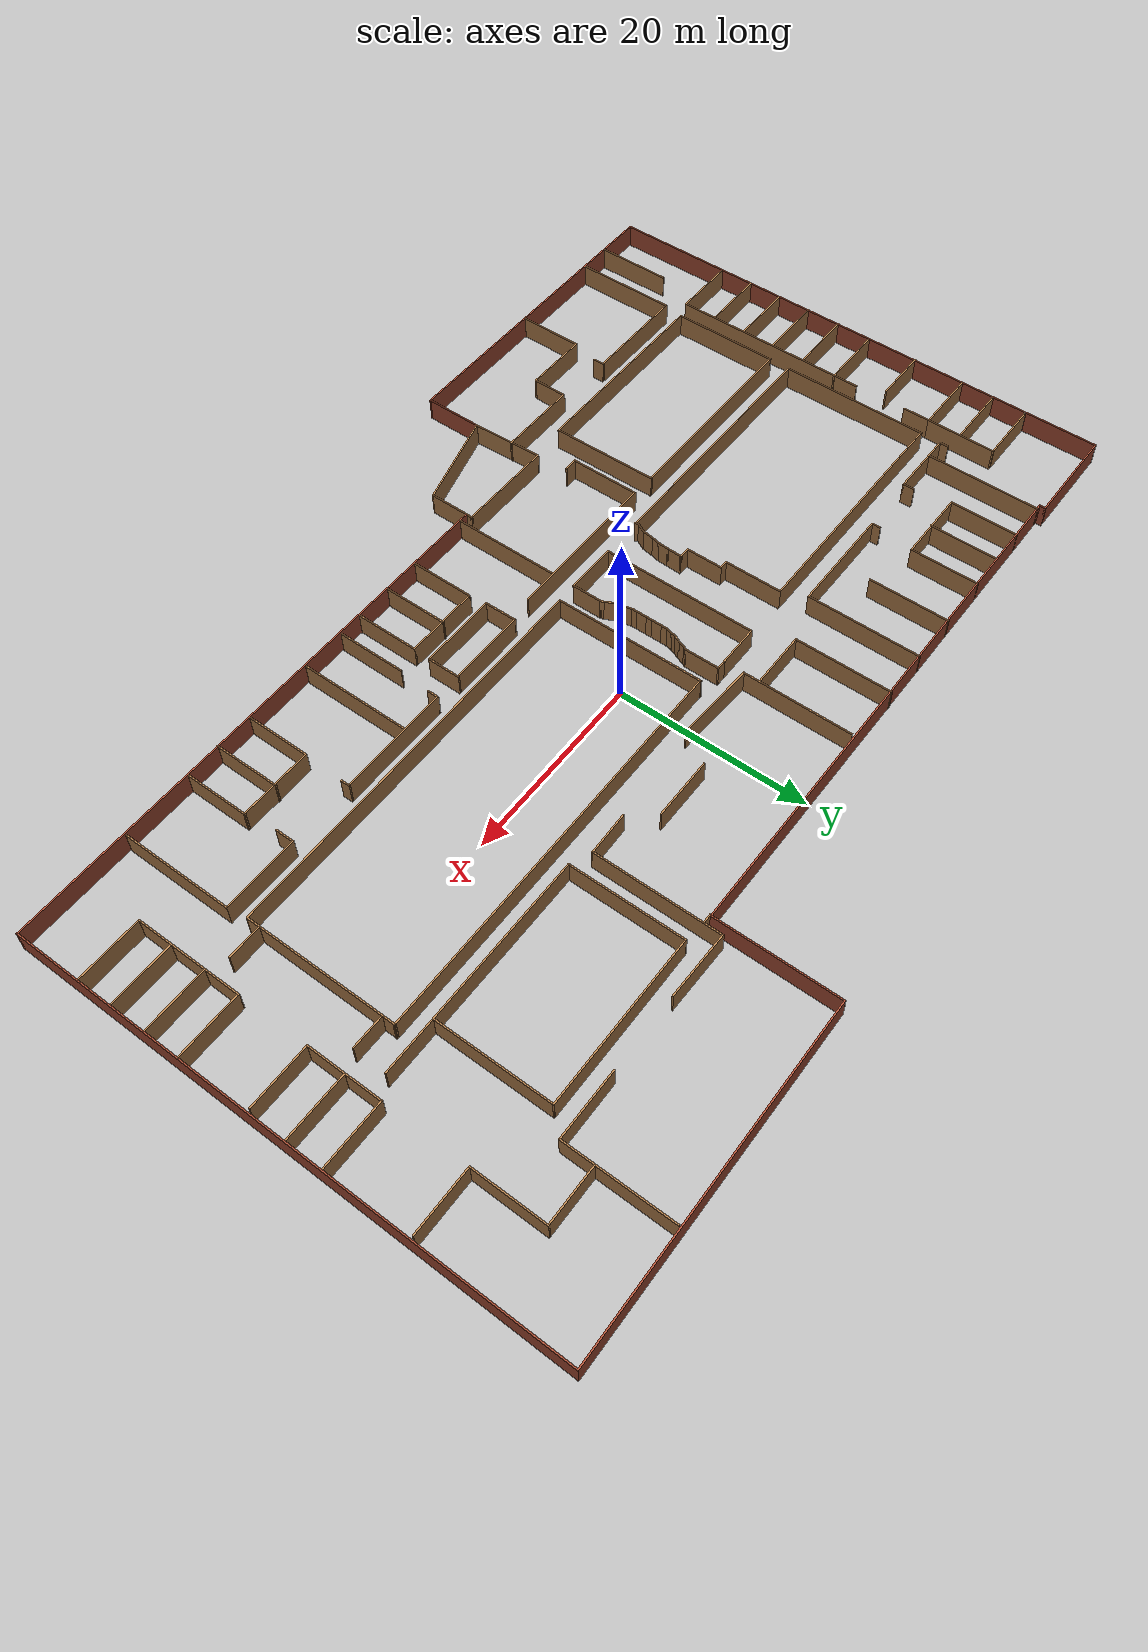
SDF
<?xml version='1.0'?>
<sdf version='1.6'>
  <model name='floorPlan'>
    <pose frame=''>-1.03517 -1.87284 0 0 -0 0</pose>
    <link name='Wall_101'>
      <collision name='Wall_101_Collision'>
        <geometry>
          <box>
            <size>10.75 0.15 2.5</size>
          </box>
        </geometry>
        <pose frame=''>0 0 1.25 0 -0 0</pose>
      </collision>
      <visual name='Wall_101_Visual'>
        <pose frame=''>0 0 1.25 0 -0 0</pose>
        <geometry>
          <box>
            <size>10.75 0.15 2.5</size>
          </box>
        </geometry>
        <material>
          <script>
            <uri>file://media/materials/scripts/gazebo.material</uri>
            <name>Gazebo/Bricks</name>
          </script>
          <ambient>1 1 1 1</ambient>
        </material>
        <meta>
          <layer>0</layer>
        </meta>
      </visual>
      <pose frame=''>-45.3755 22.7356 0 0 -0 0</pose>
    </link>
    <link name='Wall_102'>
      <collision name='Wall_102_Collision'>
        <geometry>
          <box>
            <size>0.75 0.15 2.5</size>
          </box>
        </geometry>
        <pose frame=''>0 0 1.25 0 -0 0</pose>
      </collision>
      <visual name='Wall_102_Visual'>
        <pose frame=''>0 0 1.25 0 -0 0</pose>
        <geometry>
          <box>
            <size>0.75 0.15 2.5</size>
          </box>
        </geometry>
        <material>
          <script>
            <uri>file://media/materials/scripts/gazebo.material</uri>
            <name>Gazebo/Bricks</name>
          </script>
          <ambient>1 1 1 1</ambient>
        </material>
        <meta>
          <layer>0</layer>
        </meta>
      </visual>
      <pose frame=''>-40.0755 22.4356 0 0 0 -1.5708</pose>
    </link>
    <link name='Wall_103'>
      <collision name='Wall_103_Collision'>
        <geometry>
          <box>
            <size>56.25 0.15 2.5</size>
          </box>
        </geometry>
        <pose frame=''>0 0 1.25 0 -0 0</pose>
      </collision>
      <visual name='Wall_103_Visual'>
        <pose frame=''>0 0 1.25 0 -0 0</pose>
        <geometry>
          <box>
            <size>56.25 0.15 2.5</size>
          </box>
        </geometry>
        <material>
          <script>
            <uri>file://media/materials/scripts/gazebo.material</uri>
            <name>Gazebo/Bricks</name>
          </script>
          <ambient>1 1 1 1</ambient>
        </material>
        <meta>
          <layer>0</layer>
        </meta>
      </visual>
      <pose frame=''>-12.0255 22.1356 0 0 -0 0</pose>
    </link>
    <link name='Wall_105'>
      <collision name='Wall_105_Collision'>
        <geometry>
          <box>
            <size>13 0.15 2.5</size>
          </box>
        </geometry>
        <pose frame=''>0 0 1.25 0 -0 0</pose>
      </collision>
      <visual name='Wall_105_Visual'>
        <pose frame=''>0 0 1.25 0 -0 0</pose>
        <geometry>
          <box>
            <size>13 0.15 2.5</size>
          </box>
        </geometry>
        <material>
          <script>
            <uri>file://media/materials/scripts/gazebo.material</uri>
            <name>Gazebo/Bricks</name>
          </script>
          <ambient>1 1 1 1</ambient>
        </material>
        <meta>
          <layer>0</layer>
        </meta>
      </visual>
      <pose frame=''>16.1718 28.4394 0 0 0 -1.5708</pose>
    </link>
    <link name='Wall_107'>
      <collision name='Wall_107_Collision'>
        <geometry>
          <box>
            <size>1 0.15 2.5</size>
          </box>
        </geometry>
        <pose frame=''>0 0 1.25 0 -0 0</pose>
      </collision>
      <visual name='Wall_107_Visual'>
        <pose frame=''>0 0 1.25 0 -0 0</pose>
        <geometry>
          <box>
            <size>1 0.15 2.5</size>
          </box>
        </geometry>
        <material>
          <script>
            <uri>file://media/materials/scripts/gazebo.material</uri>
            <name>Gazebo/Wood</name>
          </script>
          <ambient>1 1 1 1</ambient>
        </material>
        <meta>
          <layer>0</layer>
        </meta>
      </visual>
      <pose frame=''>16.5968 22.0144 0 0 -0 0</pose>
    </link>
    <link name='Wall_109'>
      <collision name='Wall_109_Collision'>
        <geometry>
          <box>
            <size>11.75 0.15 2.5</size>
          </box>
        </geometry>
        <pose frame=''>0 0 1.25 0 -0 0</pose>
      </collision>
      <visual name='Wall_109_Visual'>
        <pose frame=''>0 0 1.25 0 -0 0</pose>
        <geometry>
          <box>
            <size>11.75 0.15 2.5</size>
          </box>
        </geometry>
        <material>
          <script>
            <uri>file://media/materials/scripts/gazebo.material</uri>
            <name>Gazebo/Wood</name>
          </script>
          <ambient>1 1 1 1</ambient>
        </material>
        <meta>
          <layer>0</layer>
        </meta>
      </visual>
      <pose frame=''>39.004 -15.7975 0 0 0 -1.5708</pose>
    </link>
    <link name='Wall_111'>
      <collision name='Wall_111_Collision'>
        <geometry>
          <box>
            <size>8 0.15 2.5</size>
          </box>
        </geometry>
        <pose frame=''>0 0 1.25 0 -0 0</pose>
      </collision>
      <visual name='Wall_111_Visual'>
        <pose frame=''>0 0 1.25 0 -0 0</pose>
        <geometry>
          <box>
            <size>8 0.15 2.5</size>
          </box>
        </geometry>
        <material>
          <script>
            <uri>file://media/materials/scripts/gazebo.material</uri>
            <name>Gazebo/Wood</name>
          </script>
          <ambient>1 1 1 1</ambient>
        </material>
        <meta>
          <layer>0</layer>
        </meta>
      </visual>
      <pose frame=''>35.079 -9.99746 0 0 -0 3.14159</pose>
    </link>
    <link name='Wall_112'>
      <collision name='Wall_112_Collision'>
        <geometry>
          <box>
            <size>2 0.15 2.5</size>
          </box>
        </geometry>
        <pose frame=''>0 0 1.25 0 -0 0</pose>
      </collision>
      <visual name='Wall_112_Visual'>
        <pose frame=''>0 0 1.25 0 -0 0</pose>
        <geometry>
          <box>
            <size>2 0.15 2.5</size>
          </box>
        </geometry>
        <material>
          <script>
            <uri>file://media/materials/scripts/gazebo.material</uri>
            <name>Gazebo/Wood</name>
          </script>
          <ambient>1 1 1 1</ambient>
        </material>
        <meta>
          <layer>0</layer>
        </meta>
      </visual>
      <pose frame=''>31.154 -10.9225 0 0 0 -1.5708</pose>
    </link>
    <link name='Wall_114'>
      <collision name='Wall_114_Collision'>
        <geometry>
          <box>
            <size>6.75 0.15 2.5</size>
          </box>
        </geometry>
        <pose frame=''>0 0 1.25 0 -0 0</pose>
      </collision>
      <visual name='Wall_114_Visual'>
        <pose frame=''>0 0 1.25 0 -0 0</pose>
        <geometry>
          <box>
            <size>6.75 0.15 2.5</size>
          </box>
        </geometry>
        <material>
          <script>
            <uri>file://media/materials/scripts/gazebo.material</uri>
            <name>Gazebo/Wood</name>
          </script>
          <ambient>1 1 1 1</ambient>
        </material>
        <meta>
          <layer>0</layer>
        </meta>
      </visual>
      <pose frame=''>31.5938 -18.4328 0 0 -0 1.5708</pose>
    </link>
    <link name='Wall_115'>
      <collision name='Wall_115_Collision'>
        <geometry>
          <box>
            <size>7.75 0.15 2.5</size>
          </box>
        </geometry>
        <pose frame=''>0 0 1.25 0 -0 0</pose>
      </collision>
      <visual name='Wall_115_Visual'>
        <pose frame=''>0 0 1.25 0 -0 0</pose>
        <geometry>
          <box>
            <size>7.75 0.15 2.5</size>
          </box>
        </geometry>
        <material>
          <script>
            <uri>file://media/materials/scripts/gazebo.material</uri>
            <name>Gazebo/Wood</name>
          </script>
          <ambient>1 1 1 1</ambient>
        </material>
        <meta>
          <layer>0</layer>
        </meta>
      </visual>
      <pose frame=''>27.7938 -15.1328 0 0 -0 3.14159</pose>
    </link>
    <link name='Wall_116'>
      <collision name='Wall_116_Collision'>
        <geometry>
          <box>
            <size>6.75 0.15 2.5</size>
          </box>
        </geometry>
        <pose frame=''>0 0 1.25 0 -0 0</pose>
      </collision>
      <visual name='Wall_116_Visual'>
        <pose frame=''>0 0 1.25 0 -0 0</pose>
        <geometry>
          <box>
            <size>6.75 0.15 2.5</size>
          </box>
        </geometry>
        <material>
          <script>
            <uri>file://media/materials/scripts/gazebo.material</uri>
            <name>Gazebo/Wood</name>
          </script>
          <ambient>1 1 1 1</ambient>
        </material>
        <meta>
          <layer>0</layer>
        </meta>
      </visual>
      <pose frame=''>23.9938 -18.4328 0 0 0 -1.5708</pose>
    </link>
    <link name='Wall_118'>
      <collision name='Wall_118_Collision'>
        <geometry>
          <box>
            <size>1 0.15 2.5</size>
          </box>
        </geometry>
        <pose frame=''>0 0 1.25 0 -0 0</pose>
      </collision>
      <visual name='Wall_118_Visual'>
        <pose frame=''>0 0 1.25 0 -0 0</pose>
        <geometry>
          <box>
            <size>1 0.15 2.5</size>
          </box>
        </geometry>
        <material>
          <script>
            <uri>file://media/materials/scripts/gazebo.material</uri>
            <name>Gazebo/Wood</name>
          </script>
          <ambient>1 1 1 1</ambient>
        </material>
        <meta>
          <layer>0</layer>
        </meta>
      </visual>
      <pose frame=''>24.1778 -10.3922 0 0 0 -1.5708</pose>
    </link>
    <link name='Wall_120'>
      <collision name='Wall_120_Collision'>
        <geometry>
          <box>
            <size>11.75 0.15 2.5</size>
          </box>
        </geometry>
        <pose frame=''>0 0 1.25 0 -0 0</pose>
      </collision>
      <visual name='Wall_120_Visual'>
        <pose frame=''>0 0 1.25 0 -0 0</pose>
        <geometry>
          <box>
            <size>11.75 0.15 2.5</size>
          </box>
        </geometry>
        <material>
          <script>
            <uri>file://media/materials/scripts/gazebo.material</uri>
            <name>Gazebo/Wood</name>
          </script>
          <ambient>1 1 1 1</ambient>
        </material>
        <meta>
          <layer>0</layer>
        </meta>
      </visual>
      <pose frame=''>18.2324 -9.96721 0 0 -0 3.14159</pose>
    </link>
    <link name='Wall_121'>
      <collision name='Wall_121_Collision'>
        <geometry>
          <box>
            <size>1.25 0.15 2.5</size>
          </box>
        </geometry>
        <pose frame=''>0 0 1.25 0 -0 0</pose>
      </collision>
      <visual name='Wall_121_Visual'>
        <pose frame=''>0 0 1.25 0 -0 0</pose>
        <geometry>
          <box>
            <size>1.25 0.15 2.5</size>
          </box>
        </geometry>
        <material>
          <script>
            <uri>file://media/materials/scripts/gazebo.material</uri>
            <name>Gazebo/Wood</name>
          </script>
          <ambient>1 1 1 1</ambient>
        </material>
        <meta>
          <layer>0</layer>
        </meta>
      </visual>
      <pose frame=''>12.4324 -10.5172 0 0 0 -1.5708</pose>
    </link>
    <link name='Wall_123'>
      <collision name='Wall_123_Collision'>
        <geometry>
          <box>
            <size>11.75 0.15 2.5</size>
          </box>
        </geometry>
        <pose frame=''>0 0 1.25 0 -0 0</pose>
      </collision>
      <visual name='Wall_123_Visual'>
        <pose frame=''>0 0 1.25 0 -0 0</pose>
        <geometry>
          <box>
            <size>11.75 0.15 2.5</size>
          </box>
        </geometry>
        <material>
          <script>
            <uri>file://media/materials/scripts/gazebo.material</uri>
            <name>Gazebo/Wood</name>
          </script>
          <ambient>1 1 1 1</ambient>
        </material>
        <meta>
          <layer>0</layer>
        </meta>
      </visual>
      <pose frame=''>16.8339 -15.8579 0 0 0 -1.5708</pose>
    </link>
    <link name='Wall_125'>
      <collision name='Wall_125_Collision'>
        <geometry>
          <box>
            <size>7.25 0.15 2.5</size>
          </box>
        </geometry>
        <pose frame=''>0 0 1.25 0 -0 0</pose>
      </collision>
      <visual name='Wall_125_Visual'>
        <pose frame=''>0 0 1.25 0 -0 0</pose>
        <geometry>
          <box>
            <size>7.25 0.15 2.5</size>
          </box>
        </geometry>
        <material>
          <script>
            <uri>file://media/materials/scripts/gazebo.material</uri>
            <name>Gazebo/Wood</name>
          </script>
          <ambient>1 1 1 1</ambient>
        </material>
        <meta>
          <layer>0</layer>
        </meta>
      </visual>
      <pose frame=''>12.1458 -18.0541 0 0 0 -1.5708</pose>
    </link>
    <link name='Wall_127'>
      <collision name='Wall_127_Collision'>
        <geometry>
          <box>
            <size>11.5 0.15 2.5</size>
          </box>
        </geometry>
        <pose frame=''>0 0 1.25 0 -0 0</pose>
      </collision>
      <visual name='Wall_127_Visual'>
        <pose frame=''>0 0 1.25 0 -0 0</pose>
        <geometry>
          <box>
            <size>11.5 0.15 2.5</size>
          </box>
        </geometry>
        <material>
          <script>
            <uri>file://media/materials/scripts/gazebo.material</uri>
            <name>Gazebo/Wood</name>
          </script>
          <ambient>1 1 1 1</ambient>
        </material>
        <meta>
          <layer>0</layer>
        </meta>
      </visual>
      <pose frame=''>-5.05877 -16.1593 0 0 0 -1.5708</pose>
    </link>
    <link name='Wall_129'>
      <collision name='Wall_129_Collision'>
        <geometry>
          <box>
            <size>17 0.15 2.5</size>
          </box>
        </geometry>
        <pose frame=''>0 0 1.25 0 -0 0</pose>
      </collision>
      <visual name='Wall_129_Visual'>
        <pose frame=''>0 0 1.25 0 -0 0</pose>
        <geometry>
          <box>
            <size>17 0.15 2.5</size>
          </box>
        </geometry>
        <material>
          <script>
            <uri>file://media/materials/scripts/gazebo.material</uri>
            <name>Gazebo/Wood</name>
          </script>
          <ambient>1 1 1 1</ambient>
        </material>
        <meta>
          <layer>0</layer>
        </meta>
      </visual>
      <pose frame=''>-9.61757 -10.458 0 0 -0 3.14159</pose>
    </link>
    <link name='Wall_130'>
      <collision name='Wall_130_Collision'>
        <geometry>
          <box>
            <size>7.5 0.15 2.5</size>
          </box>
        </geometry>
        <pose frame=''>0 0 1.25 0 -0 0</pose>
      </collision>
      <visual name='Wall_130_Visual'>
        <pose frame=''>0 0 1.25 0 -0 0</pose>
        <geometry>
          <box>
            <size>7.5 0.15 2.5</size>
          </box>
        </geometry>
        <material>
          <script>
            <uri>file://media/materials/scripts/gazebo.material</uri>
            <name>Gazebo/Wood</name>
          </script>
          <ambient>1 1 1 1</ambient>
        </material>
        <meta>
          <layer>0</layer>
        </meta>
      </visual>
      <pose frame=''>-18.0426 -14.133 0 0 0 -1.5708</pose>
    </link>
    <link name='Wall_131'>
      <collision name='Wall_131_Collision'>
        <geometry>
          <box>
            <size>1.5 0.15 2.5</size>
          </box>
        </geometry>
        <pose frame=''>0 0 1.25 0 -0 0</pose>
      </collision>
      <visual name='Wall_131_Visual'>
        <pose frame=''>0 0 1.25 0 -0 0</pose>
        <geometry>
          <box>
            <size>1.5 0.15 2.5</size>
          </box>
        </geometry>
        <material>
          <script>
            <uri>file://media/materials/scripts/gazebo.material</uri>
            <name>Gazebo/Wood</name>
          </script>
          <ambient>1 1 1 1</ambient>
        </material>
        <meta>
          <layer>0</layer>
        </meta>
      </visual>
      <pose frame=''>-17.3676 -17.808 0 0 -0 0</pose>
    </link>
    <link name='Wall_133'>
      <collision name='Wall_133_Collision'>
        <geometry>
          <box>
            <size>10.5 0.15 2.5</size>
          </box>
        </geometry>
        <pose frame=''>0 0 1.25 0 -0 0</pose>
      </collision>
      <visual name='Wall_133_Visual'>
        <pose frame=''>0 0 1.25 0 -0 0</pose>
        <geometry>
          <box>
            <size>10.5 0.15 2.5</size>
          </box>
        </geometry>
        <material>
          <script>
            <uri>file://media/materials/scripts/gazebo.material</uri>
            <name>Gazebo/Wood</name>
          </script>
          <ambient>1 1 1 1</ambient>
        </material>
        <meta>
          <layer>0</layer>
        </meta>
      </visual>
      <pose frame=''>-11.2193 -21.215 0 0 -0 0</pose>
    </link>
    <link name='Wall_134'>
      <collision name='Wall_134_Collision'>
        <geometry>
          <box>
            <size>0.822713 0.15 2.5</size>
          </box>
        </geometry>
        <pose frame=''>0 0 1.25 0 -0 0</pose>
      </collision>
      <visual name='Wall_134_Visual'>
        <pose frame=''>0 0 1.25 0 -0 0</pose>
        <geometry>
          <box>
            <size>0.822713 0.15 2.5</size>
          </box>
        </geometry>
        <material>
          <script>
            <uri>file://media/materials/scripts/gazebo.material</uri>
            <name>Gazebo/Wood</name>
          </script>
          <ambient>1 1 1 1</ambient>
        </material>
        <meta>
          <layer>0</layer>
        </meta>
      </visual>
      <pose frame=''>-6.06127 -21.5509 0 0 0 -1.62113</pose>
    </link>
    <link name='Wall_137'>
      <collision name='Wall_137_Collision'>
        <geometry>
          <box>
            <size>7.70614 0.15 2.5</size>
          </box>
        </geometry>
        <pose frame=''>0 0 1.25 0 -0 0</pose>
      </collision>
      <visual name='Wall_137_Visual'>
        <pose frame=''>0 0 1.25 0 -0 0</pose>
        <geometry>
          <box>
            <size>7.70614 0.15 2.5</size>
          </box>
        </geometry>
        <material>
          <script>
            <uri>file://media/materials/scripts/gazebo.material</uri>
            <name>Gazebo/Wood</name>
          </script>
          <ambient>1 1 1 1</ambient>
        </material>
        <meta>
          <layer>0</layer>
        </meta>
      </visual>
      <pose frame=''>-16.2349 -24.9897 0 0 0 -1.52859</pose>
    </link>
    <link name='Wall_139'>
      <collision name='Wall_139_Collision'>
        <geometry>
          <box>
            <size>8.75 0.15 2.5</size>
          </box>
        </geometry>
        <pose frame=''>0 0 1.25 0 -0 0</pose>
      </collision>
      <visual name='Wall_139_Visual'>
        <pose frame=''>0 0 1.25 0 -0 0</pose>
        <geometry>
          <box>
            <size>8.75 0.15 2.5</size>
          </box>
        </geometry>
        <material>
          <script>
            <uri>file://media/materials/scripts/gazebo.material</uri>
            <name>Gazebo/Wood</name>
          </script>
          <ambient>1 1 1 1</ambient>
        </material>
        <meta>
          <layer>0</layer>
        </meta>
      </visual>
      <pose frame=''>-20.4877 -24.4086 0 0 -0 3.14159</pose>
    </link>
    <link name='Wall_140'>
      <collision name='Wall_140_Collision'>
        <geometry>
          <box>
            <size>3.75 0.15 2.5</size>
          </box>
        </geometry>
        <pose frame=''>0 0 1.25 0 -0 0</pose>
      </collision>
      <visual name='Wall_140_Visual'>
        <pose frame=''>0 0 1.25 0 -0 0</pose>
        <geometry>
          <box>
            <size>3.75 0.15 2.5</size>
          </box>
        </geometry>
        <material>
          <script>
            <uri>file://media/materials/scripts/gazebo.material</uri>
            <name>Gazebo/Wood</name>
          </script>
          <ambient>1 1 1 1</ambient>
        </material>
        <meta>
          <layer>0</layer>
        </meta>
      </visual>
      <pose frame=''>-24.7877 -26.2086 0 0 0 -1.5708</pose>
    </link>
    <link name='Wall_141'>
      <collision name='Wall_141_Collision'>
        <geometry>
          <box>
            <size>7 0.15 2.5</size>
          </box>
        </geometry>
        <pose frame=''>0 0 1.25 0 -0 0</pose>
      </collision>
      <visual name='Wall_141_Visual'>
        <pose frame=''>0 0 1.25 0 -0 0</pose>
        <geometry>
          <box>
            <size>7 0.15 2.5</size>
          </box>
        </geometry>
        <material>
          <script>
            <uri>file://media/materials/scripts/gazebo.material</uri>
            <name>Gazebo/Wood</name>
          </script>
          <ambient>1 1 1 1</ambient>
        </material>
        <meta>
          <layer>0</layer>
        </meta>
      </visual>
      <pose frame=''>-28.2127 -28.0086 0 0 -0 3.14159</pose>
    </link>
    <link name='Wall_142'>
      <collision name='Wall_142_Collision'>
        <geometry>
          <box>
            <size>7 0.15 2.5</size>
          </box>
        </geometry>
        <pose frame=''>0 0 1.25 0 -0 0</pose>
      </collision>
      <visual name='Wall_142_Visual'>
        <pose frame=''>0 0 1.25 0 -0 0</pose>
        <geometry>
          <box>
            <size>7 0.15 2.5</size>
          </box>
        </geometry>
        <material>
          <script>
            <uri>file://media/materials/scripts/gazebo.material</uri>
            <name>Gazebo/Wood</name>
          </script>
          <ambient>1 1 1 1</ambient>
        </material>
        <meta>
          <layer>0</layer>
        </meta>
      </visual>
      <pose frame=''>-31.6377 -31.4336 0 0 0 -1.5708</pose>
    </link>
    <link name='Wall_144'>
      <collision name='Wall_144_Collision'>
        <geometry>
          <box>
            <size>1.25 0.15 2.5</size>
          </box>
        </geometry>
        <pose frame=''>0 0 1.25 0 -0 0</pose>
      </collision>
      <visual name='Wall_144_Visual'>
        <pose frame=''>0 0 1.25 0 -0 0</pose>
        <geometry>
          <box>
            <size>1.25 0.15 2.5</size>
          </box>
        </geometry>
        <material>
          <script>
            <uri>file://media/materials/scripts/gazebo.material</uri>
            <name>Gazebo/Wood</name>
          </script>
          <ambient>1 1 1 1</ambient>
        </material>
        <meta>
          <layer>0</layer>
        </meta>
      </visual>
      <pose frame=''>-30.9008 -24.4847 0 0 -0 1.5708</pose>
    </link>
    <link name='Wall_146'>
      <collision name='Wall_146_Collision'>
        <geometry>
          <box>
            <size>11.5 0.15 2.5</size>
          </box>
        </geometry>
        <pose frame=''>0 0 1.25 0 -0 0</pose>
      </collision>
      <visual name='Wall_146_Visual'>
        <pose frame=''>0 0 1.25 0 -0 0</pose>
        <geometry>
          <box>
            <size>11.5 0.15 2.5</size>
          </box>
        </geometry>
        <material>
          <script>
            <uri>file://media/materials/scripts/gazebo.material</uri>
            <name>Gazebo/Wood</name>
          </script>
          <ambient>1 1 1 1</ambient>
        </material>
        <meta>
          <layer>0</layer>
        </meta>
      </visual>
      <pose frame=''>-36.5758 -23.9347 0 0 -0 3.14159</pose>
    </link>
    <link name='Wall_147'>
      <collision name='Wall_147_Collision'>
        <geometry>
          <box>
            <size>11 0.15 2.5</size>
          </box>
        </geometry>
        <pose frame=''>0 0 1.25 0 -0 0</pose>
      </collision>
      <visual name='Wall_147_Visual'>
        <pose frame=''>0 0 1.25 0 -0 0</pose>
        <geometry>
          <box>
            <size>11 0.15 2.5</size>
          </box>
        </geometry>
        <material>
          <script>
            <uri>file://media/materials/scripts/gazebo.material</uri>
            <name>Gazebo/Wood</name>
          </script>
          <ambient>1 1 1 1</ambient>
        </material>
        <meta>
          <layer>0</layer>
        </meta>
      </visual>
      <pose frame=''>-42.2508 -29.3597 0 0 0 -1.5708</pose>
    </link>
    <link name='Wall_149'>
      <collision name='Wall_149_Collision'>
        <geometry>
          <box>
            <size>8 0.15 2.5</size>
          </box>
        </geometry>
        <pose frame=''>0 0 1.25 0 -0 0</pose>
      </collision>
      <visual name='Wall_149_Visual'>
        <pose frame=''>0 0 1.25 0 -0 0</pose>
        <geometry>
          <box>
            <size>8 0.15 2.5</size>
          </box>
        </geometry>
        <material>
          <script>
            <uri>file://media/materials/scripts/gazebo.material</uri>
            <name>Gazebo/Wood</name>
          </script>
          <ambient>1 1 1 1</ambient>
        </material>
        <meta>
          <layer>0</layer>
        </meta>
      </visual>
      <pose frame=''>-45.7877 -30.8032 0 0 0 -1.5708</pose>
    </link>
    <link name='Wall_151'>
      <collision name='Wall_151_Collision'>
        <geometry>
          <box>
            <size>7 0.15 2.5</size>
          </box>
        </geometry>
        <pose frame=''>0 0 1.25 0 -0 0</pose>
      </collision>
      <visual name='Wall_151_Visual'>
        <pose frame=''>0 0 1.25 0 -0 0</pose>
        <geometry>
          <box>
            <size>7 0.15 2.5</size>
          </box>
        </geometry>
        <material>
          <script>
            <uri>file://media/materials/scripts/gazebo.material</uri>
            <name>Gazebo/Wood</name>
          </script>
          <ambient>1 1 1 1</ambient>
        </material>
        <meta>
          <layer>0</layer>
        </meta>
      </visual>
      <pose frame=''>-47.1627 -22.3564 0 0 -0 0</pose>
    </link>
    <link name='Wall_152'>
      <collision name='Wall_152_Collision'>
        <geometry>
          <box>
            <size>21.5 0.15 2.5</size>
          </box>
        </geometry>
        <pose frame=''>0 0 1.25 0 -0 0</pose>
      </collision>
      <visual name='Wall_152_Visual'>
        <pose frame=''>0 0 1.25 0 -0 0</pose>
        <geometry>
          <box>
            <size>21.5 0.15 2.5</size>
          </box>
        </geometry>
        <material>
          <script>
            <uri>file://media/materials/scripts/gazebo.material</uri>
            <name>Gazebo/Wood</name>
          </script>
          <ambient>1 1 1 1</ambient>
        </material>
        <meta>
          <layer>0</layer>
        </meta>
      </visual>
      <pose frame=''>-43.7377 -11.6814 0 0 -0 1.5708</pose>
    </link>
    <link name='Wall_154'>
      <collision name='Wall_154_Collision'>
        <geometry>
          <box>
            <size>11.5 0.15 2.5</size>
          </box>
        </geometry>
        <pose frame=''>0 0 1.25 0 -0 0</pose>
      </collision>
      <visual name='Wall_154_Visual'>
        <pose frame=''>0 0 1.25 0 -0 0</pose>
        <geometry>
          <box>
            <size>11.5 0.15 2.5</size>
          </box>
        </geometry>
        <material>
          <script>
            <uri>file://media/materials/scripts/gazebo.material</uri>
            <name>Gazebo/Wood</name>
          </script>
          <ambient>1 1 1 1</ambient>
        </material>
        <meta>
          <layer>0</layer>
        </meta>
      </visual>
      <pose frame=''>-20.5182 -16.0314 0 0 0 -1.5616</pose>
    </link>
    <link name='Wall_155'>
      <collision name='Wall_155_Collision'>
        <geometry>
          <box>
            <size>21.5 0.15 2.5</size>
          </box>
        </geometry>
        <pose frame=''>0 0 1.25 0 -0 0</pose>
      </collision>
      <visual name='Wall_155_Visual'>
        <pose frame=''>0 0 1.25 0 -0 0</pose>
        <geometry>
          <box>
            <size>21.5 0.15 2.5</size>
          </box>
        </geometry>
        <material>
          <script>
            <uri>file://media/materials/scripts/gazebo.material</uri>
            <name>Gazebo/Wood</name>
          </script>
          <ambient>1 1 1 1</ambient>
        </material>
        <meta>
          <layer>0</layer>
        </meta>
      </visual>
      <pose frame=''>-31.1758 -21.7064 0 0 -0 3.14159</pose>
    </link>
    <link name='Wall_158'>
      <collision name='Wall_158_Collision'>
        <geometry>
          <box>
            <size>11.5 0.15 2.5</size>
          </box>
        </geometry>
        <pose frame=''>0 0 1.25 0 -0 0</pose>
      </collision>
      <visual name='Wall_158_Visual'>
        <pose frame=''>0 0 1.25 0 -0 0</pose>
        <geometry>
          <box>
            <size>11.5 0.15 2.5</size>
          </box>
        </geometry>
        <material>
          <script>
            <uri>file://media/materials/scripts/gazebo.material</uri>
            <name>Gazebo/Wood</name>
          </script>
          <ambient>1 1 1 1</ambient>
        </material>
        <meta>
          <layer>0</layer>
        </meta>
      </visual>
      <pose frame=''>-41.8508 -16.0314 0 0 -0 1.5708</pose>
    </link>
    <link name='Wall_159'>
      <collision name='Wall_159_Collision'>
        <geometry>
          <box>
            <size>21.25 0.15 2.5</size>
          </box>
        </geometry>
        <pose frame=''>0 0 1.25 0 -0 0</pose>
      </collision>
      <visual name='Wall_159_Visual'>
        <pose frame=''>0 0 1.25 0 -0 0</pose>
        <geometry>
          <box>
            <size>21.25 0.15 2.5</size>
          </box>
        </geometry>
        <material>
          <script>
            <uri>file://media/materials/scripts/gazebo.material</uri>
            <name>Gazebo/Wood</name>
          </script>
          <ambient>1 1 1 1</ambient>
        </material>
        <meta>
          <layer>0</layer>
        </meta>
      </visual>
      <pose frame=''>-31.3008 -10.3564 0 0 -0 0</pose>
    </link>
    <link name='Wall_161'>
      <collision name='Wall_161_Collision'>
        <geometry>
          <box>
            <size>5 0.15 2.5</size>
          </box>
        </geometry>
        <pose frame=''>0 0 1.25 0 -0 0</pose>
      </collision>
      <visual name='Wall_161_Visual'>
        <pose frame=''>0 0 1.25 0 -0 0</pose>
        <geometry>
          <box>
            <size>5 0.15 2.5</size>
          </box>
        </geometry>
        <material>
          <script>
            <uri>file://media/materials/scripts/gazebo.material</uri>
            <name>Gazebo/Wood</name>
          </script>
          <ambient>1 1 1 1</ambient>
        </material>
        <meta>
          <layer>0</layer>
        </meta>
      </visual>
      <pose frame=''>-7.97942 8.30014 0 0 -0 3.14159</pose>
    </link>
    <link name='Wall_162'>
      <collision name='Wall_162_Collision'>
        <geometry>
          <box>
            <size>16.5 0.15 2.5</size>
          </box>
        </geometry>
        <pose frame=''>0 0 1.25 0 -0 0</pose>
      </collision>
      <visual name='Wall_162_Visual'>
        <pose frame=''>0 0 1.25 0 -0 0</pose>
        <geometry>
          <box>
            <size>16.5 0.15 2.5</size>
          </box>
        </geometry>
        <material>
          <script>
            <uri>file://media/materials/scripts/gazebo.material</uri>
            <name>Gazebo/Wood</name>
          </script>
          <ambient>1 1 1 1</ambient>
        </material>
        <meta>
          <layer>0</layer>
        </meta>
      </visual>
      <pose frame=''>-10.4044 0.125141 0 0 0 -1.5708</pose>
    </link>
    <link name='Wall_163'>
      <collision name='Wall_163_Collision'>
        <geometry>
          <box>
            <size>5.5 0.15 2.5</size>
          </box>
        </geometry>
        <pose frame=''>0 0 1.25 0 -0 0</pose>
      </collision>
      <visual name='Wall_163_Visual'>
        <pose frame=''>0 0 1.25 0 -0 0</pose>
        <geometry>
          <box>
            <size>5.5 0.15 2.5</size>
          </box>
        </geometry>
        <material>
          <script>
            <uri>file://media/materials/scripts/gazebo.material</uri>
            <name>Gazebo/Wood</name>
          </script>
          <ambient>1 1 1 1</ambient>
        </material>
        <meta>
          <layer>0</layer>
        </meta>
      </visual>
      <pose frame=''>-7.72942 -8.04986 0 0 -0 0</pose>
    </link>
    <link name='Wall_164'>
      <collision name='Wall_164_Collision'>
        <geometry>
          <box>
            <size>3.25 0.15 2.5</size>
          </box>
        </geometry>
        <pose frame=''>0 0 1.25 0 -0 0</pose>
      </collision>
      <visual name='Wall_164_Visual'>
        <pose frame=''>0 0 1.25 0 -0 0</pose>
        <geometry>
          <box>
            <size>3.25 0.15 2.5</size>
          </box>
        </geometry>
        <material>
          <script>
            <uri>file://media/materials/scripts/gazebo.material</uri>
            <name>Gazebo/Wood</name>
          </script>
          <ambient>1 1 1 1</ambient>
        </material>
        <meta>
          <layer>0</layer>
        </meta>
      </visual>
      <pose frame=''>-5.05442 -6.49986 0 0 -0 1.5708</pose>
    </link>
    <link name='Wall_165'>
      <collision name='Wall_165_Collision'>
        <geometry>
          <box>
            <size>0.5 0.15 2.5</size>
          </box>
        </geometry>
        <pose frame=''>0 0 1.25 0 -0 0</pose>
      </collision>
      <visual name='Wall_165_Visual'>
        <pose frame=''>0 0 1.25 0 -0 0</pose>
        <geometry>
          <box>
            <size>0.5 0.15 2.5</size>
          </box>
        </geometry>
        <material>
          <script>
            <uri>file://media/materials/scripts/gazebo.material</uri>
            <name>Gazebo/Wood</name>
          </script>
          <ambient>1 1 1 1</ambient>
        </material>
        <meta>
          <layer>0</layer>
        </meta>
      </visual>
      <pose frame=''>-5.09971 -4.78082 0 0 -0 1.8326</pose>
    </link>
    <link name='Wall_166'>
      <collision name='Wall_166_Collision'>
        <geometry>
          <box>
            <size>1.5 0.15 2.5</size>
          </box>
        </geometry>
        <pose frame=''>0 0 1.25 0 -0 0</pose>
      </collision>
      <visual name='Wall_166_Visual'>
        <pose frame=''>0 0 1.25 0 -0 0</pose>
        <geometry>
          <box>
            <size>1.5 0.15 2.5</size>
          </box>
        </geometry>
        <material>
          <script>
            <uri>file://media/materials/scripts/gazebo.material</uri>
            <name>Gazebo/Wood</name>
          </script>
          <ambient>1 1 1 1</ambient>
        </material>
        <meta>
          <layer>0</layer>
        </meta>
      </visual>
      <pose frame=''>-5.4825 -4.02722 0 0 -0 2.0944</pose>
    </link>
    <link name='Wall_167'>
      <collision name='Wall_167_Collision'>
        <geometry>
          <box>
            <size>0.75 0.15 2.5</size>
          </box>
        </geometry>
        <pose frame=''>0 0 1.25 0 -0 0</pose>
      </collision>
      <visual name='Wall_167_Visual'>
        <pose frame=''>0 0 1.25 0 -0 0</pose>
        <geometry>
          <box>
            <size>0.75 0.15 2.5</size>
          </box>
        </geometry>
        <material>
          <script>
            <uri>file://media/materials/scripts/gazebo.material</uri>
            <name>Gazebo/Wood</name>
          </script>
          <ambient>1 1 1 1</ambient>
        </material>
        <meta>
          <layer>0</layer>
        </meta>
      </visual>
      <pose frame=''>-5.82 -3.14265 0 0 -0 1.5708</pose>
    </link>
    <link name='Wall_168'>
      <collision name='Wall_168_Collision'>
        <geometry>
          <box>
            <size>1 0.15 2.5</size>
          </box>
        </geometry>
        <pose frame=''>0 0 1.25 0 -0 0</pose>
      </collision>
      <visual name='Wall_168_Visual'>
        <pose frame=''>0 0 1.25 0 -0 0</pose>
        <geometry>
          <box>
            <size>1 0.15 2.5</size>
          </box>
        </geometry>
        <material>
          <script>
            <uri>file://media/materials/scripts/gazebo.material</uri>
            <name>Gazebo/Wood</name>
          </script>
          <ambient>1 1 1 1</ambient>
        </material>
        <meta>
          <layer>0</layer>
        </meta>
      </visual>
      <pose frame=''>-5.93 -2.43213 0 0 -0 1.8326</pose>
    </link>
    <link name='Wall_169'>
      <collision name='Wall_169_Collision'>
        <geometry>
          <box>
            <size>0.75 0.15 2.5</size>
          </box>
        </geometry>
        <pose frame=''>0 0 1.25 0 -0 0</pose>
      </collision>
      <visual name='Wall_169_Visual'>
        <pose frame=''>0 0 1.25 0 -0 0</pose>
        <geometry>
          <box>
            <size>0.75 0.15 2.5</size>
          </box>
        </geometry>
        <material>
          <script>
            <uri>file://media/materials/scripts/gazebo.material</uri>
            <name>Gazebo/Wood</name>
          </script>
          <ambient>1 1 1 1</ambient>
        </material>
        <meta>
          <layer>0</layer>
        </meta>
      </visual>
      <pose frame=''>-6.04 -1.72161 0 0 -0 1.5708</pose>
    </link>
    <link name='Wall_170'>
      <collision name='Wall_170_Collision'>
        <geometry>
          <box>
            <size>1.25 0.15 2.5</size>
          </box>
        </geometry>
        <pose frame=''>0 0 1.25 0 -0 0</pose>
      </collision>
      <visual name='Wall_170_Visual'>
        <pose frame=''>0 0 1.25 0 -0 0</pose>
        <geometry>
          <box>
            <size>1.25 0.15 2.5</size>
          </box>
        </geometry>
        <material>
          <script>
            <uri>file://media/materials/scripts/gazebo.material</uri>
            <name>Gazebo/Wood</name>
          </script>
          <ambient>1 1 1 1</ambient>
        </material>
        <meta>
          <layer>0</layer>
        </meta>
      </visual>
      <pose frame=''>-6.04 -0.871614 0 0 -0 1.5708</pose>
    </link>
    <link name='Wall_171'>
      <collision name='Wall_171_Collision'>
        <geometry>
          <box>
            <size>0.75 0.15 2.5</size>
          </box>
        </geometry>
        <pose frame=''>0 0 1.25 0 -0 0</pose>
      </collision>
      <visual name='Wall_171_Visual'>
        <pose frame=''>0 0 1.25 0 -0 0</pose>
        <geometry>
          <box>
            <size>0.75 0.15 2.5</size>
          </box>
        </geometry>
        <material>
          <script>
            <uri>file://media/materials/scripts/gazebo.material</uri>
            <name>Gazebo/Wood</name>
          </script>
          <ambient>1 1 1 1</ambient>
        </material>
        <meta>
          <layer>0</layer>
        </meta>
      </visual>
      <pose frame=''>-6.04 -0.021614 0 0 -0 1.5708</pose>
    </link>
    <link name='Wall_172'>
      <collision name='Wall_172_Collision'>
        <geometry>
          <box>
            <size>1.25 0.15 2.5</size>
          </box>
        </geometry>
        <pose frame=''>0 0 1.25 0 -0 0</pose>
      </collision>
      <visual name='Wall_172_Visual'>
        <pose frame=''>0 0 1.25 0 -0 0</pose>
        <geometry>
          <box>
            <size>1.25 0.15 2.5</size>
          </box>
        </geometry>
        <material>
          <script>
            <uri>file://media/materials/scripts/gazebo.material</uri>
            <name>Gazebo/Wood</name>
          </script>
          <ambient>1 1 1 1</ambient>
        </material>
        <meta>
          <layer>0</layer>
        </meta>
      </visual>
      <pose frame=''>-6.04 0.828386 0 0 -0 1.5708</pose>
    </link>
    <link name='Wall_173'>
      <collision name='Wall_173_Collision'>
        <geometry>
          <box>
            <size>0.75 0.15 2.5</size>
          </box>
        </geometry>
        <pose frame=''>0 0 1.25 0 -0 0</pose>
      </collision>
      <visual name='Wall_173_Visual'>
        <pose frame=''>0 0 1.25 0 -0 0</pose>
        <geometry>
          <box>
            <size>0.75 0.15 2.5</size>
          </box>
        </geometry>
        <material>
          <script>
            <uri>file://media/materials/scripts/gazebo.material</uri>
            <name>Gazebo/Wood</name>
          </script>
          <ambient>1 1 1 1</ambient>
        </material>
        <meta>
          <layer>0</layer>
        </meta>
      </visual>
      <pose frame=''>-6.04 1.67839 0 0 -0 1.5708</pose>
    </link>
    <link name='Wall_174'>
      <collision name='Wall_174_Collision'>
        <geometry>
          <box>
            <size>0.75 0.15 2.5</size>
          </box>
        </geometry>
        <pose frame=''>0 0 1.25 0 -0 0</pose>
      </collision>
      <visual name='Wall_174_Visual'>
        <pose frame=''>0 0 1.25 0 -0 0</pose>
        <geometry>
          <box>
            <size>0.75 0.15 2.5</size>
          </box>
        </geometry>
        <material>
          <script>
            <uri>file://media/materials/scripts/gazebo.material</uri>
            <name>Gazebo/Wood</name>
          </script>
          <ambient>1 1 1 1</ambient>
        </material>
        <meta>
          <layer>0</layer>
        </meta>
      </visual>
      <pose frame=''>-5.96235 2.26816 0 0 -0 1.309</pose>
    </link>
    <link name='Wall_175'>
      <collision name='Wall_175_Collision'>
        <geometry>
          <box>
            <size>0.68871 0.15 2.5</size>
          </box>
        </geometry>
        <pose frame=''>0 0 1.25 0 -0 0</pose>
      </collision>
      <visual name='Wall_175_Visual'>
        <pose frame=''>0 0 1.25 0 -0 0</pose>
        <geometry>
          <box>
            <size>0.68871 0.15 2.5</size>
          </box>
        </geometry>
        <material>
          <script>
            <uri>file://media/materials/scripts/gazebo.material</uri>
            <name>Gazebo/Wood</name>
          </script>
          <ambient>1 1 1 1</ambient>
        </material>
        <meta>
          <layer>0</layer>
        </meta>
      </visual>
      <pose frame=''>-5.82391 2.82035 0 0 -0 1.34312</pose>
    </link>
    <link name='Wall_176'>
      <collision name='Wall_176_Collision'>
        <geometry>
          <box>
            <size>0.881262 0.15 2.5</size>
          </box>
        </geometry>
        <pose frame=''>0 0 1.25 0 -0 0</pose>
      </collision>
      <visual name='Wall_176_Visual'>
        <pose frame=''>0 0 1.25 0 -0 0</pose>
        <geometry>
          <box>
            <size>0.881262 0.15 2.5</size>
          </box>
        </geometry>
        <material>
          <script>
            <uri>file://media/materials/scripts/gazebo.material</uri>
            <name>Gazebo/Wood</name>
          </script>
          <ambient>1 1 1 1</ambient>
        </material>
        <meta>
          <layer>0</layer>
        </meta>
      </visual>
      <pose frame=''>-5.60659 3.41318 0 0 -0 1.12842</pose>
    </link>
    <link name='Wall_177'>
      <collision name='Wall_177_Collision'>
        <geometry>
          <box>
            <size>0.843039 0.15 2.5</size>
          </box>
        </geometry>
        <pose frame=''>0 0 1.25 0 -0 0</pose>
      </collision>
      <visual name='Wall_177_Visual'>
        <pose frame=''>0 0 1.25 0 -0 0</pose>
        <geometry>
          <box>
            <size>0.843039 0.15 2.5</size>
          </box>
        </geometry>
        <material>
          <script>
            <uri>file://media/materials/scripts/gazebo.material</uri>
            <name>Gazebo/Wood</name>
          </script>
          <ambient>1 1 1 1</ambient>
        </material>
        <meta>
          <layer>0</layer>
        </meta>
      </visual>
      <pose frame=''>-5.34572 4.07405 0 0 -0 1.26492</pose>
    </link>
    <link name='Wall_178'>
      <collision name='Wall_178_Collision'>
        <geometry>
          <box>
            <size>0.5 0.15 2.5</size>
          </box>
        </geometry>
        <pose frame=''>0 0 1.25 0 -0 0</pose>
      </collision>
      <visual name='Wall_178_Visual'>
        <pose frame=''>0 0 1.25 0 -0 0</pose>
        <geometry>
          <box>
            <size>0.5 0.15 2.5</size>
          </box>
        </geometry>
        <material>
          <script>
            <uri>file://media/materials/scripts/gazebo.material</uri>
            <name>Gazebo/Wood</name>
          </script>
          <ambient>1 1 1 1</ambient>
        </material>
        <meta>
          <layer>0</layer>
        </meta>
      </visual>
      <pose frame=''>-5.15387 4.55604 0 0 -0 1.0472</pose>
    </link>
    <link name='Wall_179'>
      <collision name='Wall_179_Collision'>
        <geometry>
          <box>
            <size>3.75 0.15 2.5</size>
          </box>
        </geometry>
        <pose frame=''>0 0 1.25 0 -0 0</pose>
      </collision>
      <visual name='Wall_179_Visual'>
        <pose frame=''>0 0 1.25 0 -0 0</pose>
        <geometry>
          <box>
            <size>3.75 0.15 2.5</size>
          </box>
        </geometry>
        <material>
          <script>
            <uri>file://media/materials/scripts/gazebo.material</uri>
            <name>Gazebo/Wood</name>
          </script>
          <ambient>1 1 1 1</ambient>
        </material>
        <meta>
          <layer>0</layer>
        </meta>
      </visual>
      <pose frame=''>-5.06637 6.5076 0 0 -0 1.5708</pose>
    </link>
    <link name='Wall_180'>
      <collision name='Wall_180_Collision'>
        <geometry>
          <box>
            <size>1 0.15 2.5</size>
          </box>
        </geometry>
        <pose frame=''>0 0 1.25 0 -0 0</pose>
      </collision>
      <visual name='Wall_180_Visual'>
        <pose frame=''>0 0 1.25 0 -0 0</pose>
        <geometry>
          <box>
            <size>1 0.15 2.5</size>
          </box>
        </geometry>
        <material>
          <script>
            <uri>file://media/materials/scripts/gazebo.material</uri>
            <name>Gazebo/Wood</name>
          </script>
          <ambient>1 1 1 1</ambient>
        </material>
        <meta>
          <layer>0</layer>
        </meta>
      </visual>
      <pose frame=''>-5.49137 8.3076 0 0 -0 3.14159</pose>
    </link>
    <link name='Wall_182'>
      <collision name='Wall_182_Collision'>
        <geometry>
          <box>
            <size>27 0.15 2.5</size>
          </box>
        </geometry>
        <pose frame=''>0 0 1.25 0 -0 0</pose>
      </collision>
      <visual name='Wall_182_Visual'>
        <pose frame=''>0 0 1.25 0 -0 0</pose>
        <geometry>
          <box>
            <size>27 0.15 2.5</size>
          </box>
        </geometry>
        <material>
          <script>
            <uri>file://media/materials/scripts/gazebo.material</uri>
            <name>Gazebo/Wood</name>
          </script>
          <ambient>1 1 1 1</ambient>
        </material>
        <meta>
          <layer>0</layer>
        </meta>
      </visual>
      <pose frame=''>-28.3707 -8.0129 0 0 -0 3.14159</pose>
    </link>
    <link name='Wall_184'>
      <collision name='Wall_184_Collision'>
        <geometry>
          <box>
            <size>16 0.15 2.5</size>
          </box>
        </geometry>
        <pose frame=''>0 0 1.25 0 -0 0</pose>
      </collision>
      <visual name='Wall_184_Visual'>
        <pose frame=''>0 0 1.25 0 -0 0</pose>
        <geometry>
          <box>
            <size>16 0.15 2.5</size>
          </box>
        </geometry>
        <material>
          <script>
            <uri>file://media/materials/scripts/gazebo.material</uri>
            <name>Gazebo/Wood</name>
          </script>
          <ambient>1 1 1 1</ambient>
        </material>
        <meta>
          <layer>0</layer>
        </meta>
      </visual>
      <pose frame=''>-41.7957 -0.087903 0 0 -0 1.5708</pose>
    </link>
    <link name='Wall_185'>
      <collision name='Wall_185_Collision'>
        <geometry>
          <box>
            <size>26 0.15 2.5</size>
          </box>
        </geometry>
        <pose frame=''>0 0 1.25 0 -0 0</pose>
      </collision>
      <visual name='Wall_185_Visual'>
        <pose frame=''>0 0 1.25 0 -0 0</pose>
        <geometry>
          <box>
            <size>26 0.15 2.5</size>
          </box>
        </geometry>
        <material>
          <script>
            <uri>file://media/materials/scripts/gazebo.material</uri>
            <name>Gazebo/Wood</name>
          </script>
          <ambient>1 1 1 1</ambient>
        </material>
        <meta>
          <layer>0</layer>
        </meta>
      </visual>
      <pose frame=''>-28.8707 7.8371 0 0 -0 0</pose>
    </link>
    <link name='Wall_186'>
      <collision name='Wall_186_Collision'>
        <geometry>
          <box>
            <size>6.25 0.15 2.5</size>
          </box>
        </geometry>
        <pose frame=''>0 0 1.25 0 -0 0</pose>
      </collision>
      <visual name='Wall_186_Visual'>
        <pose frame=''>0 0 1.25 0 -0 0</pose>
        <geometry>
          <box>
            <size>6.25 0.15 2.5</size>
          </box>
        </geometry>
        <material>
          <script>
            <uri>file://media/materials/scripts/gazebo.material</uri>
            <name>Gazebo/Wood</name>
          </script>
          <ambient>1 1 1 1</ambient>
        </material>
        <meta>
          <layer>0</layer>
        </meta>
      </visual>
      <pose frame=''>-15.9457 4.7871 0 0 0 -1.5708</pose>
    </link>
    <link name='Wall_187'>
      <collision name='Wall_187_Collision'>
        <geometry>
          <box>
            <size>1 0.15 2.5</size>
          </box>
        </geometry>
        <pose frame=''>0 0 1.25 0 -0 0</pose>
      </collision>
      <visual name='Wall_187_Visual'>
        <pose frame=''>0 0 1.25 0 -0 0</pose>
        <geometry>
          <box>
            <size>1 0.15 2.5</size>
          </box>
        </geometry>
        <material>
          <script>
            <uri>file://media/materials/scripts/gazebo.material</uri>
            <name>Gazebo/Wood</name>
          </script>
          <ambient>1 1 1 1</ambient>
        </material>
        <meta>
          <layer>0</layer>
        </meta>
      </visual>
      <pose frame=''>-15.5207 1.7371 0 0 -0 0</pose>
    </link>
    <link name='Wall_188'>
      <collision name='Wall_188_Collision'>
        <geometry>
          <box>
            <size>4 0.15 2.5</size>
          </box>
        </geometry>
        <pose frame=''>0 0 1.25 0 -0 0</pose>
      </collision>
      <visual name='Wall_188_Visual'>
        <pose frame=''>0 0 1.25 0 -0 0</pose>
        <geometry>
          <box>
            <size>4 0.15 2.5</size>
          </box>
        </geometry>
        <material>
          <script>
            <uri>file://media/materials/scripts/gazebo.material</uri>
            <name>Gazebo/Wood</name>
          </script>
          <ambient>1 1 1 1</ambient>
        </material>
        <meta>
          <layer>0</layer>
        </meta>
      </visual>
      <pose frame=''>-15.0957 -0.187903 0 0 0 -1.5708</pose>
    </link>
    <link name='Wall_189'>
      <collision name='Wall_189_Collision'>
        <geometry>
          <box>
            <size>1.25 0.15 2.5</size>
          </box>
        </geometry>
        <pose frame=''>0 0 1.25 0 -0 0</pose>
      </collision>
      <visual name='Wall_189_Visual'>
        <pose frame=''>0 0 1.25 0 -0 0</pose>
        <geometry>
          <box>
            <size>1.25 0.15 2.5</size>
          </box>
        </geometry>
        <material>
          <script>
            <uri>file://media/materials/scripts/gazebo.material</uri>
            <name>Gazebo/Wood</name>
          </script>
          <ambient>1 1 1 1</ambient>
        </material>
        <meta>
          <layer>0</layer>
        </meta>
      </visual>
      <pose frame=''>-14.5457 -2.1129 0 0 -0 0</pose>
    </link>
    <link name='Wall_190'>
      <collision name='Wall_190_Collision'>
        <geometry>
          <box>
            <size>1.66808 0.15 2.5</size>
          </box>
        </geometry>
        <pose frame=''>0 0 1.25 0 -0 0</pose>
      </collision>
      <visual name='Wall_190_Visual'>
        <pose frame=''>0 0 1.25 0 -0 0</pose>
        <geometry>
          <box>
            <size>1.66808 0.15 2.5</size>
          </box>
        </geometry>
        <material>
          <script>
            <uri>file://media/materials/scripts/gazebo.material</uri>
            <name>Gazebo/Wood</name>
          </script>
          <ambient>1 1 1 1</ambient>
        </material>
        <meta>
          <layer>0</layer>
        </meta>
      </visual>
      <pose frame=''>-14.0185 -2.8716 0 0 0 -1.60087</pose>
    </link>
    <link name='Wall_191'>
      <collision name='Wall_191_Collision'>
        <geometry>
          <box>
            <size>1.33465 0.15 2.5</size>
          </box>
        </geometry>
        <pose frame=''>0 0 1.25 0 -0 0</pose>
      </collision>
      <visual name='Wall_191_Visual'>
        <pose frame=''>0 0 1.25 0 -0 0</pose>
        <geometry>
          <box>
            <size>1.33465 0.15 2.5</size>
          </box>
        </geometry>
        <material>
          <script>
            <uri>file://media/materials/scripts/gazebo.material</uri>
            <name>Gazebo/Wood</name>
          </script>
          <ambient>1 1 1 1</ambient>
        </material>
        <meta>
          <layer>0</layer>
        </meta>
      </visual>
      <pose frame=''>-14.0762 -4.2216 0 0 0 -1.62955</pose>
    </link>
    <link name='Wall_192'>
      <collision name='Wall_192_Collision'>
        <geometry>
          <box>
            <size>0.968685 0.15 2.5</size>
          </box>
        </geometry>
        <pose frame=''>0 0 1.25 0 -0 0</pose>
      </collision>
      <visual name='Wall_192_Visual'>
        <pose frame=''>0 0 1.25 0 -0 0</pose>
        <geometry>
          <box>
            <size>0.968685 0.15 2.5</size>
          </box>
        </geometry>
        <material>
          <script>
            <uri>file://media/materials/scripts/gazebo.material</uri>
            <name>Gazebo/Wood</name>
          </script>
          <ambient>1 1 1 1</ambient>
        </material>
        <meta>
          <layer>0</layer>
        </meta>
      </visual>
      <pose frame=''>-14.1979 -5.2129 0 0 0 -1.78486</pose>
    </link>
    <link name='Wall_193'>
      <collision name='Wall_193_Collision'>
        <geometry>
          <box>
            <size>1.37975 0.15 2.5</size>
          </box>
        </geometry>
        <pose frame=''>0 0 1.25 0 -0 0</pose>
      </collision>
      <visual name='Wall_193_Visual'>
        <pose frame=''>0 0 1.25 0 -0 0</pose>
        <geometry>
          <box>
            <size>1.37975 0.15 2.5</size>
          </box>
        </geometry>
        <material>
          <script>
            <uri>file://media/materials/scripts/gazebo.material</uri>
            <name>Gazebo/Wood</name>
          </script>
          <ambient>1 1 1 1</ambient>
        </material>
        <meta>
          <layer>0</layer>
        </meta>
      </visual>
      <pose frame=''>-14.3718 -6.2216 0 0 0 -1.71269</pose>
    </link>
    <link name='Wall_194'>
      <collision name='Wall_194_Collision'>
        <geometry>
          <box>
            <size>1.20787 0.15 2.5</size>
          </box>
        </geometry>
        <pose frame=''>0 0 1.25 0 -0 0</pose>
      </collision>
      <visual name='Wall_194_Visual'>
        <pose frame=''>0 0 1.25 0 -0 0</pose>
        <geometry>
          <box>
            <size>1.20787 0.15 2.5</size>
          </box>
        </geometry>
        <material>
          <script>
            <uri>file://media/materials/scripts/gazebo.material</uri>
            <name>Gazebo/Wood</name>
          </script>
          <ambient>1 1 1 1</ambient>
        </material>
        <meta>
          <layer>0</layer>
        </meta>
      </visual>
      <pose frame=''>-14.7022 -7.29986 0 0 0 -2.04915</pose>
    </link>
    <link name='Wall_195'>
      <collision name='Wall_195_Collision'>
        <geometry>
          <box>
            <size>0.479977 0.15 2.5</size>
          </box>
        </geometry>
        <pose frame=''>0 0 1.25 0 -0 0</pose>
      </collision>
      <visual name='Wall_195_Visual'>
        <pose frame=''>0 0 1.25 0 -0 0</pose>
        <geometry>
          <box>
            <size>0.479977 0.15 2.5</size>
          </box>
        </geometry>
        <material>
          <script>
            <uri>file://media/materials/scripts/gazebo.material</uri>
            <name>Gazebo/Wood</name>
          </script>
          <ambient>1 1 1 1</ambient>
        </material>
        <meta>
          <layer>0</layer>
        </meta>
      </visual>
      <pose frame=''>-14.8935 -7.92595 0 0 0 -1.24905</pose>
    </link>
    <link name='Wall_198'>
      <collision name='Wall_198_Collision'>
        <geometry>
          <box>
            <size>6 0.15 2.5</size>
          </box>
        </geometry>
        <pose frame=''>0 0 1.25 0 -0 0</pose>
      </collision>
      <visual name='Wall_198_Visual'>
        <pose frame=''>0 0 1.25 0 -0 0</pose>
        <geometry>
          <box>
            <size>6 0.15 2.5</size>
          </box>
        </geometry>
        <material>
          <script>
            <uri>file://media/materials/scripts/gazebo.material</uri>
            <name>Gazebo/Wood</name>
          </script>
          <ambient>1 1 1 1</ambient>
        </material>
        <meta>
          <layer>0</layer>
        </meta>
      </visual>
      <pose frame=''>-47.8468 1.90014 0 0 -0 0</pose>
    </link>
    <link name='Wall_200'>
      <collision name='Wall_200_Collision'>
        <geometry>
          <box>
            <size>3 0.15 2.5</size>
          </box>
        </geometry>
        <pose frame=''>0 0 1.25 0 -0 0</pose>
      </collision>
      <visual name='Wall_200_Visual'>
        <pose frame=''>0 0 1.25 0 -0 0</pose>
        <geometry>
          <box>
            <size>3 0.15 2.5</size>
          </box>
        </geometry>
        <material>
          <script>
            <uri>file://media/materials/scripts/gazebo.material</uri>
            <name>Gazebo/Wood</name>
          </script>
          <ambient>1 1 1 1</ambient>
        </material>
        <meta>
          <layer>0</layer>
        </meta>
      </visual>
      <pose frame=''>-43.8501 6.14253 0 0 -0 1.5708</pose>
    </link>
    <link name='Wall_201'>
      <collision name='Wall_201_Collision'>
        <geometry>
          <box>
            <size>7 0.15 2.5</size>
          </box>
        </geometry>
        <pose frame=''>0 0 1.25 0 -0 0</pose>
      </collision>
      <visual name='Wall_201_Visual'>
        <pose frame=''>0 0 1.25 0 -0 0</pose>
        <geometry>
          <box>
            <size>7 0.15 2.5</size>
          </box>
        </geometry>
        <material>
          <script>
            <uri>file://media/materials/scripts/gazebo.material</uri>
            <name>Gazebo/Wood</name>
          </script>
          <ambient>1 1 1 1</ambient>
        </material>
        <meta>
          <layer>0</layer>
        </meta>
      </visual>
      <pose frame=''>-47.2751 7.56753 0 0 -0 3.14159</pose>
    </link>
    <link name='Wall_204'>
      <collision name='Wall_204_Collision'>
        <geometry>
          <box>
            <size>7.5 0.15 2.5</size>
          </box>
        </geometry>
        <pose frame=''>0 0 1.25 0 -0 0</pose>
      </collision>
      <visual name='Wall_204_Visual'>
        <pose frame=''>0 0 1.25 0 -0 0</pose>
        <geometry>
          <box>
            <size>7.5 0.15 2.5</size>
          </box>
        </geometry>
        <material>
          <script>
            <uri>file://media/materials/scripts/gazebo.material</uri>
            <name>Gazebo/Wood</name>
          </script>
          <ambient>1 1 1 1</ambient>
        </material>
        <meta>
          <layer>0</layer>
        </meta>
      </visual>
      <pose frame=''>-43.8501 11.2425 0 0 -0 1.5708</pose>
    </link>
    <link name='Wall_205'>
      <collision name='Wall_205_Collision'>
        <geometry>
          <box>
            <size>6.75 0.15 2.5</size>
          </box>
        </geometry>
        <pose frame=''>0 0 1.25 0 -0 0</pose>
      </collision>
      <visual name='Wall_205_Visual'>
        <pose frame=''>0 0 1.25 0 -0 0</pose>
        <geometry>
          <box>
            <size>6.75 0.15 2.5</size>
          </box>
        </geometry>
        <material>
          <script>
            <uri>file://media/materials/scripts/gazebo.material</uri>
            <name>Gazebo/Wood</name>
          </script>
          <ambient>1 1 1 1</ambient>
        </material>
        <meta>
          <layer>0</layer>
        </meta>
      </visual>
      <pose frame=''>-47.1501 14.9175 0 0 -0 3.14159</pose>
    </link>
    <link name='Wall_207'>
      <collision name='Wall_207_Collision'>
        <geometry>
          <box>
            <size>0.25 0.15 2.5</size>
          </box>
        </geometry>
        <pose frame=''>0 0 1.25 0 -0 0</pose>
      </collision>
      <visual name='Wall_207_Visual'>
        <pose frame=''>0 0 1.25 0 -0 0</pose>
        <geometry>
          <box>
            <size>0.25 0.15 2.5</size>
          </box>
        </geometry>
        <material>
          <script>
            <uri>file://media/materials/scripts/gazebo.material</uri>
            <name>Gazebo/Grey</name>
          </script>
          <ambient>1 1 1 1</ambient>
        </material>
        <meta>
          <layer>0</layer>
        </meta>
      </visual>
      <pose frame=''>-50.5001 14.9175 0 0 -0 3.14159</pose>
    </link>
    <link name='Wall_209'>
      <collision name='Wall_209_Collision'>
        <geometry>
          <box>
            <size>7.25 0.15 2.5</size>
          </box>
        </geometry>
        <pose frame=''>0 0 1.25 0 -0 0</pose>
      </collision>
      <visual name='Wall_209_Visual'>
        <pose frame=''>0 0 1.25 0 -0 0</pose>
        <geometry>
          <box>
            <size>7.25 0.15 2.5</size>
          </box>
        </geometry>
        <material>
          <script>
            <uri>file://media/materials/scripts/gazebo.material</uri>
            <name>Gazebo/Wood</name>
          </script>
          <ambient>1 1 1 1</ambient>
        </material>
        <meta>
          <layer>0</layer>
        </meta>
      </visual>
      <pose frame=''>-38.2131 10.0741 0 0 -0 0</pose>
    </link>
    <link name='Wall_210'>
      <collision name='Wall_210_Collision'>
        <geometry>
          <box>
            <size>1.25 0.15 2.5</size>
          </box>
        </geometry>
        <pose frame=''>0 0 1.25 0 -0 0</pose>
      </collision>
      <visual name='Wall_210_Visual'>
        <pose frame=''>0 0 1.25 0 -0 0</pose>
        <geometry>
          <box>
            <size>1.25 0.15 2.5</size>
          </box>
        </geometry>
        <material>
          <script>
            <uri>file://media/materials/scripts/gazebo.material</uri>
            <name>Gazebo/Wood</name>
          </script>
          <ambient>1 1 1 1</ambient>
        </material>
        <meta>
          <layer>0</layer>
        </meta>
      </visual>
      <pose frame=''>-34.6631 10.6241 0 0 -0 1.5708</pose>
    </link>
    <link name='Wall_212'>
      <collision name='Wall_212_Collision'>
        <geometry>
          <box>
            <size>1 0.15 2.5</size>
          </box>
        </geometry>
        <pose frame=''>0 0 1.25 0 -0 0</pose>
      </collision>
      <visual name='Wall_212_Visual'>
        <pose frame=''>0 0 1.25 0 -0 0</pose>
        <geometry>
          <box>
            <size>1 0.15 2.5</size>
          </box>
        </geometry>
        <material>
          <script>
            <uri>file://media/materials/scripts/gazebo.material</uri>
            <name>Gazebo/Wood</name>
          </script>
          <ambient>1 1 1 1</ambient>
        </material>
        <meta>
          <layer>0</layer>
        </meta>
      </visual>
      <pose frame=''>-41.7631 10.4991 0 0 -0 1.5708</pose>
    </link>
    <link name='Wall_214'>
      <collision name='Wall_214_Collision'>
        <geometry>
          <box>
            <size>12.25 0.15 2.5</size>
          </box>
        </geometry>
        <pose frame=''>0 0 1.25 0 -0 0</pose>
      </collision>
      <visual name='Wall_214_Visual'>
        <pose frame=''>0 0 1.25 0 -0 0</pose>
        <geometry>
          <box>
            <size>12.25 0.15 2.5</size>
          </box>
        </geometry>
        <material>
          <script>
            <uri>file://media/materials/scripts/gazebo.material</uri>
            <name>Gazebo/Wood</name>
          </script>
          <ambient>1 1 1 1</ambient>
        </material>
        <meta>
          <layer>0</layer>
        </meta>
      </visual>
      <pose frame=''>-39.537 16.0936 0 0 0 -1.5708</pose>
    </link>
    <link name='Wall_216'>
      <collision name='Wall_216_Collision'>
        <geometry>
          <box>
            <size>7.25 0.15 2.5</size>
          </box>
        </geometry>
        <pose frame=''>0 0 1.25 0 -0 0</pose>
      </collision>
      <visual name='Wall_216_Visual'>
        <pose frame=''>0 0 1.25 0 -0 0</pose>
        <geometry>
          <box>
            <size>7.25 0.15 2.5</size>
          </box>
        </geometry>
        <material>
          <script>
            <uri>file://media/materials/scripts/gazebo.material</uri>
            <name>Gazebo/Wood</name>
          </script>
          <ambient>1 1 1 1</ambient>
        </material>
        <meta>
          <layer>0</layer>
        </meta>
      </visual>
      <pose frame=''>-35.3283 18.5936 0 0 0 -1.5708</pose>
    </link>
    <link name='Wall_217'>
      <collision name='Wall_217_Collision'>
        <geometry>
          <box>
            <size>7.75 0.15 2.5</size>
          </box>
        </geometry>
        <pose frame=''>0 0 1.25 0 -0 0</pose>
      </collision>
      <visual name='Wall_217_Visual'>
        <pose frame=''>0 0 1.25 0 -0 0</pose>
        <geometry>
          <box>
            <size>7.75 0.15 2.5</size>
          </box>
        </geometry>
        <material>
          <script>
            <uri>file://media/materials/scripts/gazebo.material</uri>
            <name>Gazebo/Wood</name>
          </script>
          <ambient>1 1 1 1</ambient>
        </material>
        <meta>
          <layer>0</layer>
        </meta>
      </visual>
      <pose frame=''>-31.5283 15.0436 0 0 -0 0</pose>
    </link>
    <link name='Wall_218'>
      <collision name='Wall_218_Collision'>
        <geometry>
          <box>
            <size>7.25 0.15 2.5</size>
          </box>
        </geometry>
        <pose frame=''>0 0 1.25 0 -0 0</pose>
      </collision>
      <visual name='Wall_218_Visual'>
        <pose frame=''>0 0 1.25 0 -0 0</pose>
        <geometry>
          <box>
            <size>7.25 0.15 2.5</size>
          </box>
        </geometry>
        <material>
          <script>
            <uri>file://media/materials/scripts/gazebo.material</uri>
            <name>Gazebo/Wood</name>
          </script>
          <ambient>1 1 1 1</ambient>
        </material>
        <meta>
          <layer>0</layer>
        </meta>
      </visual>
      <pose frame=''>-27.7283 18.5936 0 0 -0 1.5708</pose>
    </link>
    <link name='Wall_220'>
      <collision name='Wall_220_Collision'>
        <geometry>
          <box>
            <size>1 0.15 2.5</size>
          </box>
        </geometry>
        <pose frame=''>0 0 1.25 0 -0 0</pose>
      </collision>
      <visual name='Wall_220_Visual'>
        <pose frame=''>0 0 1.25 0 -0 0</pose>
        <geometry>
          <box>
            <size>1 0.15 2.5</size>
          </box>
        </geometry>
        <material>
          <script>
            <uri>file://media/materials/scripts/gazebo.material</uri>
            <name>Gazebo/Wood</name>
          </script>
          <ambient>1 1 1 1</ambient>
        </material>
        <meta>
          <layer>0</layer>
        </meta>
      </visual>
      <pose frame=''>-28.3718 10.7273 0 0 0 -1.5708</pose>
    </link>
    <link name='Wall_221'>
      <collision name='Wall_221_Collision'>
        <geometry>
          <box>
            <size>11.5 0.15 2.5</size>
          </box>
        </geometry>
        <pose frame=''>0 0 1.25 0 -0 0</pose>
      </collision>
      <visual name='Wall_221_Visual'>
        <pose frame=''>0 0 1.25 0 -0 0</pose>
        <geometry>
          <box>
            <size>11.5 0.15 2.5</size>
          </box>
        </geometry>
        <material>
          <script>
            <uri>file://media/materials/scripts/gazebo.material</uri>
            <name>Gazebo/Wood</name>
          </script>
          <ambient>1 1 1 1</ambient>
        </material>
        <meta>
          <layer>0</layer>
        </meta>
      </visual>
      <pose frame=''>-22.6968 10.3023 0 0 -0 0</pose>
    </link>
    <link name='Wall_222'>
      <collision name='Wall_222_Collision'>
        <geometry>
          <box>
            <size>12 0.15 2.5</size>
          </box>
        </geometry>
        <pose frame=''>0 0 1.25 0 -0 0</pose>
      </collision>
      <visual name='Wall_222_Visual'>
        <pose frame=''>0 0 1.25 0 -0 0</pose>
        <geometry>
          <box>
            <size>12 0.15 2.5</size>
          </box>
        </geometry>
        <material>
          <script>
            <uri>file://media/materials/scripts/gazebo.material</uri>
            <name>Gazebo/Wood</name>
          </script>
          <ambient>1 1 1 1</ambient>
        </material>
        <meta>
          <layer>0</layer>
        </meta>
      </visual>
      <pose frame=''>-17.0218 16.2273 0 0 -0 1.5708</pose>
    </link>
    <link name='Wall_224'>
      <collision name='Wall_224_Collision'>
        <geometry>
          <box>
            <size>8.5 0.15 2.5</size>
          </box>
        </geometry>
        <pose frame=''>0 0 1.25 0 -0 0</pose>
      </collision>
      <visual name='Wall_224_Visual'>
        <pose frame=''>0 0 1.25 0 -0 0</pose>
        <geometry>
          <box>
            <size>8.5 0.15 2.5</size>
          </box>
        </geometry>
        <material>
          <script>
            <uri>file://media/materials/scripts/gazebo.material</uri>
            <name>Gazebo/Wood</name>
          </script>
          <ambient>1 1 1 1</ambient>
        </material>
        <meta>
          <layer>0</layer>
        </meta>
      </visual>
      <pose frame=''>-22.1805 18.0034 0 0 0 -1.5708</pose>
    </link>
    <link name='Wall_226'>
      <collision name='Wall_226_Collision'>
        <geometry>
          <box>
            <size>10.25 0.15 2.5</size>
          </box>
        </geometry>
        <pose frame=''>0 0 1.25 0 -0 0</pose>
      </collision>
      <visual name='Wall_226_Visual'>
        <pose frame=''>0 0 1.25 0 -0 0</pose>
        <geometry>
          <box>
            <size>10.25 0.15 2.5</size>
          </box>
        </geometry>
        <material>
          <script>
            <uri>file://media/materials/scripts/gazebo.material</uri>
            <name>Gazebo/Wood</name>
          </script>
          <ambient>1 1 1 1</ambient>
        </material>
        <meta>
          <layer>0</layer>
        </meta>
      </visual>
      <pose frame=''>-12.024 17.1632 0 0 0 -1.5708</pose>
    </link>
    <link name='Wall_227'>
      <collision name='Wall_227_Collision'>
        <geometry>
          <box>
            <size>6 0.15 2.5</size>
          </box>
        </geometry>
        <pose frame=''>0 0 1.25 0 -0 0</pose>
      </collision>
      <visual name='Wall_227_Visual'>
        <pose frame=''>0 0 1.25 0 -0 0</pose>
        <geometry>
          <box>
            <size>6 0.15 2.5</size>
          </box>
        </geometry>
        <material>
          <script>
            <uri>file://media/materials/scripts/gazebo.material</uri>
            <name>Gazebo/Wood</name>
          </script>
          <ambient>1 1 1 1</ambient>
        </material>
        <meta>
          <layer>0</layer>
        </meta>
      </visual>
      <pose frame=''>-9.09898 12.1132 0 0 -0 0</pose>
    </link>
    <link name='Wall_229'>
      <collision name='Wall_229_Collision'>
        <geometry>
          <box>
            <size>6.75 0.15 2.5</size>
          </box>
        </geometry>
        <pose frame=''>0 0 1.25 0 -0 0</pose>
      </collision>
      <visual name='Wall_229_Visual'>
        <pose frame=''>0 0 1.25 0 -0 0</pose>
        <geometry>
          <box>
            <size>6.75 0.15 2.5</size>
          </box>
        </geometry>
        <material>
          <script>
            <uri>file://media/materials/scripts/gazebo.material</uri>
            <name>Gazebo/Wood</name>
          </script>
          <ambient>1 1 1 1</ambient>
        </material>
        <meta>
          <layer>0</layer>
        </meta>
      </visual>
      <pose frame=''>1.67781 -18.4351 0 0 0 -1.5708</pose>
    </link>
    <link name='Wall_23'>
      <collision name='Wall_23_Collision'>
        <geometry>
          <box>
            <size>16 0.15 2.5</size>
          </box>
        </geometry>
        <pose frame=''>0 0 1.25 0 -0 0</pose>
      </collision>
      <visual name='Wall_23_Visual'>
        <pose frame=''>0 0 1.25 0 -0 0</pose>
        <geometry>
          <box>
            <size>16 0.15 2.5</size>
          </box>
        </geometry>
        <material>
          <script>
            <uri>file://media/materials/scripts/gazebo.material</uri>
            <name>Gazebo/Wood</name>
          </script>
          <ambient>1 1 1 1</ambient>
        </material>
        <meta>
          <layer>0</layer>
        </meta>
      </visual>
      <pose frame=''>-2.91083 -0.082161 0 0 0 -1.56638</pose>
    </link>
    <link name='Wall_231'>
      <collision name='Wall_231_Collision'>
        <geometry>
          <box>
            <size>8 0.15 2.5</size>
          </box>
        </geometry>
        <pose frame=''>0 0 1.25 0 -0 0</pose>
      </collision>
      <visual name='Wall_231_Visual'>
        <pose frame=''>0 0 1.25 0 -0 0</pose>
        <geometry>
          <box>
            <size>8 0.15 2.5</size>
          </box>
        </geometry>
        <material>
          <script>
            <uri>file://media/materials/scripts/gazebo.material</uri>
            <name>Gazebo/Wood</name>
          </script>
          <ambient>1 1 1 1</ambient>
        </material>
        <meta>
          <layer>0</layer>
        </meta>
      </visual>
      <pose frame=''>5.60281 -15.1351 0 0 -0 0</pose>
    </link>
    <link name='Wall_232'>
      <collision name='Wall_232_Collision'>
        <geometry>
          <box>
            <size>6.75 0.15 2.5</size>
          </box>
        </geometry>
        <pose frame=''>0 0 1.25 0 -0 0</pose>
      </collision>
      <visual name='Wall_232_Visual'>
        <pose frame=''>0 0 1.25 0 -0 0</pose>
        <geometry>
          <box>
            <size>6.75 0.15 2.5</size>
          </box>
        </geometry>
        <material>
          <script>
            <uri>file://media/materials/scripts/gazebo.material</uri>
            <name>Gazebo/Wood</name>
          </script>
          <ambient>1 1 1 1</ambient>
        </material>
        <meta>
          <layer>0</layer>
        </meta>
      </visual>
      <pose frame=''>9.52781 -18.4351 0 0 0 -1.5708</pose>
    </link>
    <link name='Wall_234'>
      <collision name='Wall_234_Collision'>
        <geometry>
          <box>
            <size>3.5 0.15 2.5</size>
          </box>
        </geometry>
        <pose frame=''>0 0 1.25 0 -0 0</pose>
      </collision>
      <visual name='Wall_234_Visual'>
        <pose frame=''>0 0 1.25 0 -0 0</pose>
        <geometry>
          <box>
            <size>3.5 0.15 2.5</size>
          </box>
        </geometry>
        <material>
          <script>
            <uri>file://media/materials/scripts/gazebo.material</uri>
            <name>Gazebo/Wood</name>
          </script>
          <ambient>1 1 1 1</ambient>
        </material>
        <meta>
          <layer>0</layer>
        </meta>
      </visual>
      <pose frame=''>1.44911 -11.6186 0 0 0 -1.55714</pose>
    </link>
    <link name='Wall_235'>
      <collision name='Wall_235_Collision'>
        <geometry>
          <box>
            <size>8.25 0.15 2.5</size>
          </box>
        </geometry>
        <pose frame=''>0 0 1.25 0 -0 0</pose>
      </collision>
      <visual name='Wall_235_Visual'>
        <pose frame=''>0 0 1.25 0 -0 0</pose>
        <geometry>
          <box>
            <size>8.25 0.15 2.5</size>
          </box>
        </geometry>
        <material>
          <script>
            <uri>file://media/materials/scripts/gazebo.material</uri>
            <name>Gazebo/Wood</name>
          </script>
          <ambient>1 1 1 1</ambient>
        </material>
        <meta>
          <layer>0</layer>
        </meta>
      </visual>
      <pose frame=''>5.49911 -13.2936 0 0 -0 0</pose>
    </link>
    <link name='Wall_238'>
      <collision name='Wall_238_Collision'>
        <geometry>
          <box>
            <size>3.5 0.15 2.5</size>
          </box>
        </geometry>
        <pose frame=''>0 0 1.25 0 -0 0</pose>
      </collision>
      <visual name='Wall_238_Visual'>
        <pose frame=''>0 0 1.25 0 -0 0</pose>
        <geometry>
          <box>
            <size>3.5 0.15 2.5</size>
          </box>
        </geometry>
        <material>
          <script>
            <uri>file://media/materials/scripts/gazebo.material</uri>
            <name>Gazebo/Wood</name>
          </script>
          <ambient>1 1 1 1</ambient>
        </material>
        <meta>
          <layer>0</layer>
        </meta>
      </visual>
      <pose frame=''>9.61374 -11.5957 0 0 0 -1.5708</pose>
    </link>
    <link name='Wall_240'>
      <collision name='Wall_240_Collision'>
        <geometry>
          <box>
            <size>8.25 0.15 2.5</size>
          </box>
        </geometry>
        <pose frame=''>0 0 1.25 0 -0 0</pose>
      </collision>
      <visual name='Wall_240_Visual'>
        <pose frame=''>0 0 1.25 0 -0 0</pose>
        <geometry>
          <box>
            <size>8.25 0.15 2.5</size>
          </box>
        </geometry>
        <material>
          <script>
            <uri>file://media/materials/scripts/gazebo.material</uri>
            <name>Gazebo/Wood</name>
          </script>
          <ambient>1 1 1 1</ambient>
        </material>
        <meta>
          <layer>0</layer>
        </meta>
      </visual>
      <pose frame=''>5.47624 -9.94362 0 0 -0 0</pose>
    </link>
    <link name='Wall_242'>
      <collision name='Wall_242_Collision'>
        <geometry>
          <box>
            <size>6.75 0.15 2.5</size>
          </box>
        </geometry>
        <pose frame=''>0 0 1.25 0 -0 0</pose>
      </collision>
      <visual name='Wall_242_Visual'>
        <pose frame=''>0 0 1.25 0 -0 0</pose>
        <geometry>
          <box>
            <size>6.75 0.15 2.5</size>
          </box>
        </geometry>
        <material>
          <script>
            <uri>file://media/materials/scripts/gazebo.material</uri>
            <name>Gazebo/Wood</name>
          </script>
          <ambient>1 1 1 1</ambient>
        </material>
        <meta>
          <layer>0</layer>
        </meta>
      </visual>
      <pose frame=''>47.3564 -11.1866 0 0 -0 0</pose>
    </link>
    <link name='Wall_244'>
      <collision name='Wall_244_Collision'>
        <geometry>
          <box>
            <size>6.75 0.15 2.5</size>
          </box>
        </geometry>
        <pose frame=''>0 0 1.25 0 -0 0</pose>
      </collision>
      <visual name='Wall_244_Visual'>
        <pose frame=''>0 0 1.25 0 -0 0</pose>
        <geometry>
          <box>
            <size>6.75 0.15 2.5</size>
          </box>
        </geometry>
        <material>
          <script>
            <uri>file://media/materials/scripts/gazebo.material</uri>
            <name>Gazebo/Wood</name>
          </script>
          <ambient>1 1 1 1</ambient>
        </material>
        <meta>
          <layer>0</layer>
        </meta>
      </visual>
      <pose frame=''>47.3564 -7.44743 0 0 -0 0</pose>
    </link>
    <link name='Wall_246'>
      <collision name='Wall_246_Collision'>
        <geometry>
          <box>
            <size>6.75 0.15 2.5</size>
          </box>
        </geometry>
        <pose frame=''>0 0 1.25 0 -0 0</pose>
      </collision>
      <visual name='Wall_246_Visual'>
        <pose frame=''>0 0 1.25 0 -0 0</pose>
        <geometry>
          <box>
            <size>6.75 0.15 2.5</size>
          </box>
        </geometry>
        <material>
          <script>
            <uri>file://media/materials/scripts/gazebo.material</uri>
            <name>Gazebo/Wood</name>
          </script>
          <ambient>1 1 1 1</ambient>
        </material>
        <meta>
          <layer>0</layer>
        </meta>
      </visual>
      <pose frame=''>47.426 7.42213 0 0 -0 0</pose>
    </link>
    <link name='Wall_248'>
      <collision name='Wall_248_Collision'>
        <geometry>
          <box>
            <size>15.9548 0.15 2.5</size>
          </box>
        </geometry>
        <pose frame=''>0 0 1.25 0 -0 0</pose>
      </collision>
      <visual name='Wall_248_Visual'>
        <pose frame=''>0 0 1.25 0 -0 0</pose>
        <geometry>
          <box>
            <size>15.9548 0.15 2.5</size>
          </box>
        </geometry>
        <material>
          <script>
            <uri>file://media/materials/scripts/gazebo.material</uri>
            <name>Gazebo/Wood</name>
          </script>
          <ambient>1 1 1 1</ambient>
        </material>
        <meta>
          <layer>0</layer>
        </meta>
      </visual>
      <pose frame=''>38.697 -0.105323 0 0 0 -1.57178</pose>
    </link>
    <link name='Wall_250'>
      <collision name='Wall_250_Collision'>
        <geometry>
          <box>
            <size>7 0.15 2.5</size>
          </box>
        </geometry>
        <pose frame=''>0 0 1.25 0 -0 0</pose>
      </collision>
      <visual name='Wall_250_Visual'>
        <pose frame=''>0 0 1.25 0 -0 0</pose>
        <geometry>
          <box>
            <size>7 0.15 2.5</size>
          </box>
        </geometry>
        <material>
          <script>
            <uri>file://media/materials/scripts/gazebo.material</uri>
            <name>Gazebo/Wood</name>
          </script>
          <ambient>1 1 1 1</ambient>
        </material>
        <meta>
          <layer>0</layer>
        </meta>
      </visual>
      <pose frame=''>-47.1009 -3.6289 0 0 -0 0</pose>
    </link>
    <link name='Wall_253'>
      <collision name='Wall_253_Collision'>
        <geometry>
          <box>
            <size>7 0.15 2.5</size>
          </box>
        </geometry>
        <pose frame=''>0 0 1.25 0 -0 0</pose>
      </collision>
      <visual name='Wall_253_Visual'>
        <pose frame=''>0 0 1.25 0 -0 0</pose>
        <geometry>
          <box>
            <size>7 0.15 2.5</size>
          </box>
        </geometry>
        <material>
          <script>
            <uri>file://media/materials/scripts/gazebo.material</uri>
            <name>Gazebo/Wood</name>
          </script>
          <ambient>1 1 1 1</ambient>
        </material>
        <meta>
          <layer>0</layer>
        </meta>
      </visual>
      <pose frame=''>-47.3107 -7.5117 0 0 -0 0</pose>
    </link>
    <link name='Wall_255'>
      <collision name='Wall_255_Collision'>
        <geometry>
          <box>
            <size>7 0.15 2.5</size>
          </box>
        </geometry>
        <pose frame=''>0 0 1.25 0 -0 0</pose>
      </collision>
      <visual name='Wall_255_Visual'>
        <pose frame=''>0 0 1.25 0 -0 0</pose>
        <geometry>
          <box>
            <size>7 0.15 2.5</size>
          </box>
        </geometry>
        <material>
          <script>
            <uri>file://media/materials/scripts/gazebo.material</uri>
            <name>Gazebo/Wood</name>
          </script>
          <ambient>1 1 1 1</ambient>
        </material>
        <meta>
          <layer>0</layer>
        </meta>
      </visual>
      <pose frame=''>-47.3107 -11.2546 0 0 -0 0</pose>
    </link>
    <link name='Wall_257'>
      <collision name='Wall_257_Collision'>
        <geometry>
          <box>
            <size>7 0.15 2.5</size>
          </box>
        </geometry>
        <pose frame=''>0 0 1.25 0 -0 0</pose>
      </collision>
      <visual name='Wall_257_Visual'>
        <pose frame=''>0 0 1.25 0 -0 0</pose>
        <geometry>
          <box>
            <size>7 0.15 2.5</size>
          </box>
        </geometry>
        <material>
          <script>
            <uri>file://media/materials/scripts/gazebo.material</uri>
            <name>Gazebo/Wood</name>
          </script>
          <ambient>1 1 1 1</ambient>
        </material>
        <meta>
          <layer>0</layer>
        </meta>
      </visual>
      <pose frame=''>-47.2408 -14.9275 0 0 -0 0</pose>
    </link>
    <link name='Wall_259'>
      <collision name='Wall_259_Collision'>
        <geometry>
          <box>
            <size>7 0.15 2.5</size>
          </box>
        </geometry>
        <pose frame=''>0 0 1.25 0 -0 0</pose>
      </collision>
      <visual name='Wall_259_Visual'>
        <pose frame=''>0 0 1.25 0 -0 0</pose>
        <geometry>
          <box>
            <size>7 0.15 2.5</size>
          </box>
        </geometry>
        <material>
          <script>
            <uri>file://media/materials/scripts/gazebo.material</uri>
            <name>Gazebo/Wood</name>
          </script>
          <ambient>1 1 1 1</ambient>
        </material>
        <meta>
          <layer>0</layer>
        </meta>
      </visual>
      <pose frame=''>-47.2758 -18.6354 0 0 -0 0</pose>
    </link>
    <link name='Wall_261'>
      <collision name='Wall_261_Collision'>
        <geometry>
          <box>
            <size>6.75 0.15 2.5</size>
          </box>
        </geometry>
        <pose frame=''>0 0 1.25 0 -0 0</pose>
      </collision>
      <visual name='Wall_261_Visual'>
        <pose frame=''>0 0 1.25 0 -0 0</pose>
        <geometry>
          <box>
            <size>6.75 0.15 2.5</size>
          </box>
        </geometry>
        <material>
          <script>
            <uri>file://media/materials/scripts/gazebo.material</uri>
            <name>Gazebo/Wood</name>
          </script>
          <ambient>1 1 1 1</ambient>
        </material>
        <meta>
          <layer>0</layer>
        </meta>
      </visual>
      <pose frame=''>-47.2608 11.1677 0 0 -0 0</pose>
    </link>
    <link name='Wall_263'>
      <collision name='Wall_263_Collision'>
        <geometry>
          <box>
            <size>7.25 0.15 2.5</size>
          </box>
        </geometry>
        <pose frame=''>0 0 1.25 0 -0 0</pose>
      </collision>
      <visual name='Wall_263_Visual'>
        <pose frame=''>0 0 1.25 0 -0 0</pose>
        <geometry>
          <box>
            <size>7.25 0.15 2.5</size>
          </box>
        </geometry>
        <material>
          <script>
            <uri>file://media/materials/scripts/gazebo.material</uri>
            <name>Gazebo/Wood</name>
          </script>
          <ambient>1 1 1 1</ambient>
        </material>
        <meta>
          <layer>0</layer>
        </meta>
      </visual>
      <pose frame=''>-31.4967 18.5315 0 0 0 -1.5708</pose>
    </link>
    <link name='Wall_265'>
      <collision name='Wall_265_Collision'>
        <geometry>
          <box>
            <size>7 0.15 2.5</size>
          </box>
        </geometry>
        <pose frame=''>0 0 1.25 0 -0 0</pose>
      </collision>
      <visual name='Wall_265_Visual'>
        <pose frame=''>0 0 1.25 0 -0 0</pose>
        <geometry>
          <box>
            <size>7 0.15 2.5</size>
          </box>
        </geometry>
        <material>
          <script>
            <uri>file://media/materials/scripts/gazebo.material</uri>
            <name>Gazebo/Wood</name>
          </script>
          <ambient>1 1 1 1</ambient>
        </material>
        <meta>
          <layer>0</layer>
        </meta>
      </visual>
      <pose frame=''>5.58226 -18.4924 0 0 0 -1.5708</pose>
    </link>
    <link name='Wall_267'>
      <collision name='Wall_267_Collision'>
        <geometry>
          <box>
            <size>7 0.15 2.5</size>
          </box>
        </geometry>
        <pose frame=''>0 0 1.25 0 -0 0</pose>
      </collision>
      <visual name='Wall_267_Visual'>
        <pose frame=''>0 0 1.25 0 -0 0</pose>
        <geometry>
          <box>
            <size>7 0.15 2.5</size>
          </box>
        </geometry>
        <material>
          <script>
            <uri>file://media/materials/scripts/gazebo.material</uri>
            <name>Gazebo/Wood</name>
          </script>
          <ambient>1 1 1 1</ambient>
        </material>
        <meta>
          <layer>0</layer>
        </meta>
      </visual>
      <pose frame=''>27.8996 -18.4924 0 0 0 -1.5708</pose>
    </link>
    <link name='Wall_28'>
      <collision name='Wall_28_Collision'>
        <geometry>
          <box>
            <size>41.715 0.15 2.5</size>
          </box>
        </geometry>
        <pose frame=''>0 0 1.25 0 -0 0</pose>
      </collision>
      <visual name='Wall_28_Visual'>
        <pose frame=''>0 0 1.25 0 -0 0</pose>
        <geometry>
          <box>
            <size>41.715 0.15 2.5</size>
          </box>
        </geometry>
        <material>
          <script>
            <uri>file://media/materials/scripts/gazebo.material</uri>
            <name>Gazebo/Wood</name>
          </script>
          <ambient>1 1 1 1</ambient>
        </material>
        <meta>
          <layer>0</layer>
        </meta>
      </visual>
      <pose frame=''>17.9067 -8.00732 0 0 0 -8e-06</pose>
    </link>
    <link name='Wall_30'>
      <collision name='Wall_30_Collision'>
        <geometry>
          <box>
            <size>41.75 0.15 2.5</size>
          </box>
        </geometry>
        <pose frame=''>0 0 1.25 0 -0 0</pose>
      </collision>
      <visual name='Wall_30_Visual'>
        <pose frame=''>0 0 1.25 0 -0 0</pose>
        <geometry>
          <box>
            <size>41.75 0.15 2.5</size>
          </box>
        </geometry>
        <material>
          <script>
            <uri>file://media/materials/scripts/gazebo.material</uri>
            <name>Gazebo/Wood</name>
          </script>
          <ambient>1 1 1 1</ambient>
        </material>
        <meta>
          <layer>0</layer>
        </meta>
      </visual>
      <pose frame=''>17.958 7.79684 0 0 -0 3.14159</pose>
    </link>
    <link name='Wall_33'>
      <collision name='Wall_33_Collision'>
        <geometry>
          <box>
            <size>8.52175 0.15 2.5</size>
          </box>
        </geometry>
        <pose frame=''>0 0 1.25 0 -0 0</pose>
      </collision>
      <visual name='Wall_33_Visual'>
        <pose frame=''>0 0 1.25 0 -0 0</pose>
        <geometry>
          <box>
            <size>8.52175 0.15 2.5</size>
          </box>
        </geometry>
        <material>
          <script>
            <uri>file://media/materials/scripts/gazebo.material</uri>
            <name>Gazebo/Wood</name>
          </script>
          <ambient>1 1 1 1</ambient>
        </material>
        <meta>
          <layer>0</layer>
        </meta>
      </visual>
      <pose frame=''>-1.83025 10.1992 0 0 0 -0.056901</pose>
    </link>
    <link name='Wall_36'>
      <collision name='Wall_36_Collision'>
        <geometry>
          <box>
            <size>11.5 0.15 2.5</size>
          </box>
        </geometry>
        <pose frame=''>0 0 1.25 0 -0 0</pose>
      </collision>
      <visual name='Wall_36_Visual'>
        <pose frame=''>0 0 1.25 0 -0 0</pose>
        <geometry>
          <box>
            <size>11.5 0.15 2.5</size>
          </box>
        </geometry>
        <material>
          <script>
            <uri>file://media/materials/scripts/gazebo.material</uri>
            <name>Gazebo/Wood</name>
          </script>
          <ambient>1 1 1 1</ambient>
        </material>
        <meta>
          <layer>0</layer>
        </meta>
      </visual>
      <pose frame=''>-6.00935 16.1122 0 0 -0 1.5708</pose>
    </link>
    <link name='Wall_40'>
      <collision name='Wall_40_Collision'>
        <geometry>
          <box>
            <size>4.58162 0.15 2.5</size>
          </box>
        </geometry>
        <pose frame=''>0 0 1.25 0 -0 0</pose>
      </collision>
      <visual name='Wall_40_Visual'>
        <pose frame=''>0 0 1.25 0 -0 0</pose>
        <geometry>
          <box>
            <size>4.58162 0.15 2.5</size>
          </box>
        </geometry>
        <material>
          <script>
            <uri>file://media/materials/scripts/gazebo.material</uri>
            <name>Gazebo/Wood</name>
          </script>
          <ambient>1 1 1 1</ambient>
        </material>
        <meta>
          <layer>0</layer>
        </meta>
      </visual>
      <pose frame=''>14.8546 10.7422 0 0 -0 0.027081</pose>
    </link>
    <link name='Wall_41'>
      <collision name='Wall_41_Collision'>
        <geometry>
          <box>
            <size>13.25 0.15 2.5</size>
          </box>
        </geometry>
        <pose frame=''>0 0 1.25 0 -0 0</pose>
      </collision>
      <visual name='Wall_41_Visual'>
        <pose frame=''>0 0 1.25 0 -0 0</pose>
        <geometry>
          <box>
            <size>13.25 0.15 2.5</size>
          </box>
        </geometry>
        <material>
          <script>
            <uri>file://media/materials/scripts/gazebo.material</uri>
            <name>Gazebo/Wood</name>
          </script>
          <ambient>1 1 1 1</ambient>
        </material>
        <meta>
          <layer>0</layer>
        </meta>
      </visual>
      <pose frame=''>17.0696 17.3122 0 0 -0 1.5708</pose>
    </link>
    <link name='Wall_43'>
      <collision name='Wall_43_Collision'>
        <geometry>
          <box>
            <size>6.5 0.15 2.5</size>
          </box>
        </geometry>
        <pose frame=''>0 0 1.25 0 -0 0</pose>
      </collision>
      <visual name='Wall_43_Visual'>
        <pose frame=''>0 0 1.25 0 -0 0</pose>
        <geometry>
          <box>
            <size>6.5 0.15 2.5</size>
          </box>
        </geometry>
        <material>
          <script>
            <uri>file://media/materials/scripts/gazebo.material</uri>
            <name>Gazebo/Wood</name>
          </script>
          <ambient>1 1 1 1</ambient>
        </material>
        <meta>
          <layer>0</layer>
        </meta>
      </visual>
      <pose frame=''>7.4365 13.1926 0 0 -0 0</pose>
    </link>
    <link name='Wall_45'>
      <collision name='Wall_45_Collision'>
        <geometry>
          <box>
            <size>17.5 0.15 2.5</size>
          </box>
        </geometry>
        <pose frame=''>0 0 1.25 0 -0 0</pose>
      </collision>
      <visual name='Wall_45_Visual'>
        <pose frame=''>0 0 1.25 0 -0 0</pose>
        <geometry>
          <box>
            <size>17.5 0.15 2.5</size>
          </box>
        </geometry>
        <material>
          <script>
            <uri>file://media/materials/scripts/gazebo.material</uri>
            <name>Gazebo/Wood</name>
          </script>
          <ambient>1 1 1 1</ambient>
        </material>
        <meta>
          <layer>0</layer>
        </meta>
      </visual>
      <pose frame=''>27.8734 9.89578 0 0 -0 3.14159</pose>
    </link>
    <link name='Wall_46'>
      <collision name='Wall_46_Collision'>
        <geometry>
          <box>
            <size>12 0.15 2.5</size>
          </box>
        </geometry>
        <pose frame=''>0 0 1.25 0 -0 0</pose>
      </collision>
      <visual name='Wall_46_Visual'>
        <pose frame=''>0 0 1.25 0 -0 0</pose>
        <geometry>
          <box>
            <size>12 0.15 2.5</size>
          </box>
        </geometry>
        <material>
          <script>
            <uri>file://media/materials/scripts/gazebo.material</uri>
            <name>Gazebo/Wood</name>
          </script>
          <ambient>1 1 1 1</ambient>
        </material>
        <meta>
          <layer>0</layer>
        </meta>
      </visual>
      <pose frame=''>19.1984 15.8208 0 0 -0 1.5708</pose>
    </link>
    <link name='Wall_57'>
      <collision name='Wall_57_Collision'>
        <geometry>
          <box>
            <size>12 0.15 2.5</size>
          </box>
        </geometry>
        <pose frame=''>0 0 1.25 0 -0 0</pose>
      </collision>
      <visual name='Wall_57_Visual'>
        <pose frame=''>0 0 1.25 0 -0 0</pose>
        <geometry>
          <box>
            <size>12 0.15 2.5</size>
          </box>
        </geometry>
        <material>
          <script>
            <uri>file://media/materials/scripts/gazebo.material</uri>
            <name>Gazebo/Wood</name>
          </script>
          <ambient>1 1 1 1</ambient>
        </material>
        <meta>
          <layer>0</layer>
        </meta>
      </visual>
      <pose frame=''>36.5484 15.8208 0 0 -0 1.5708</pose>
    </link>
    <link name='Wall_59'>
      <collision name='Wall_59_Collision'>
        <geometry>
          <box>
            <size>17.5 0.15 2.5</size>
          </box>
        </geometry>
        <pose frame=''>0 0 1.25 0 -0 0</pose>
      </collision>
      <visual name='Wall_59_Visual'>
        <pose frame=''>0 0 1.25 0 -0 0</pose>
        <geometry>
          <box>
            <size>17.5 0.15 2.5</size>
          </box>
        </geometry>
        <material>
          <script>
            <uri>file://media/materials/scripts/gazebo.material</uri>
            <name>Gazebo/Wood</name>
          </script>
          <ambient>1 1 1 1</ambient>
        </material>
        <meta>
          <layer>0</layer>
        </meta>
      </visual>
      <pose frame=''>27.8734 21.7458 0 0 -0 0</pose>
    </link>
    <link name='Wall_61'>
      <collision name='Wall_61_Collision'>
        <geometry>
          <box>
            <size>6.92012 0.15 2.5</size>
          </box>
        </geometry>
        <pose frame=''>0 0 1.25 0 -0 0</pose>
      </collision>
      <visual name='Wall_61_Visual'>
        <pose frame=''>0 0 1.25 0 -0 0</pose>
        <geometry>
          <box>
            <size>6.92012 0.15 2.5</size>
          </box>
        </geometry>
        <material>
          <script>
            <uri>file://media/materials/scripts/gazebo.material</uri>
            <name>Gazebo/Wood</name>
          </script>
          <ambient>1 1 1 1</ambient>
        </material>
        <meta>
          <layer>0</layer>
        </meta>
      </visual>
      <pose frame=''>20.4546 23.8422 0 0 0 -0.017723</pose>
    </link>
    <link name='Wall_63'>
      <collision name='Wall_63_Collision'>
        <geometry>
          <box>
            <size>7 0.15 2.5</size>
          </box>
        </geometry>
        <pose frame=''>0 0 1.25 0 -0 0</pose>
      </collision>
      <visual name='Wall_63_Visual'>
        <pose frame=''>0 0 1.25 0 -0 0</pose>
        <geometry>
          <box>
            <size>7 0.15 2.5</size>
          </box>
        </geometry>
        <material>
          <script>
            <uri>file://media/materials/scripts/gazebo.material</uri>
            <name>Gazebo/Wood</name>
          </script>
          <ambient>1 1 1 1</ambient>
        </material>
        <meta>
          <layer>0</layer>
        </meta>
      </visual>
      <pose frame=''>35.0287 23.7786 0 0 -0 0</pose>
    </link>
    <link name='Wall_64'>
      <collision name='Wall_64_Collision'>
        <geometry>
          <box>
            <size>11 0.15 2.5</size>
          </box>
        </geometry>
        <pose frame=''>0 0 1.25 0 -0 0</pose>
      </collision>
      <visual name='Wall_64_Visual'>
        <pose frame=''>0 0 1.25 0 -0 0</pose>
        <geometry>
          <box>
            <size>11 0.15 2.5</size>
          </box>
        </geometry>
        <material>
          <script>
            <uri>file://media/materials/scripts/gazebo.material</uri>
            <name>Gazebo/Wood</name>
          </script>
          <ambient>1 1 1 1</ambient>
        </material>
        <meta>
          <layer>0</layer>
        </meta>
      </visual>
      <pose frame=''>38.4537 29.2036 0 0 -0 1.5708</pose>
    </link>
    <link name='Wall_66'>
      <collision name='Wall_66_Collision'>
        <geometry>
          <box>
            <size>5.75 0.15 2.5</size>
          </box>
        </geometry>
        <pose frame=''>0 0 1.25 0 -0 0</pose>
      </collision>
      <visual name='Wall_66_Visual'>
        <pose frame=''>0 0 1.25 0 -0 0</pose>
        <geometry>
          <box>
            <size>5.75 0.15 2.5</size>
          </box>
        </geometry>
        <material>
          <script>
            <uri>file://media/materials/scripts/gazebo.material</uri>
            <name>Gazebo/Wood</name>
          </script>
          <ambient>1 1 1 1</ambient>
        </material>
        <meta>
          <layer>0</layer>
        </meta>
      </visual>
      <pose frame=''>41.2694 27.0754 0 0 -0 0</pose>
    </link>
    <link name='Wall_67'>
      <collision name='Wall_67_Collision'>
        <geometry>
          <box>
            <size>7.5 0.15 2.5</size>
          </box>
        </geometry>
        <pose frame=''>0 0 1.25 0 -0 0</pose>
      </collision>
      <visual name='Wall_67_Visual'>
        <pose frame=''>0 0 1.25 0 -0 0</pose>
        <geometry>
          <box>
            <size>7.5 0.15 2.5</size>
          </box>
        </geometry>
        <material>
          <script>
            <uri>file://media/materials/scripts/gazebo.material</uri>
            <name>Gazebo/Wood</name>
          </script>
          <ambient>1 1 1 1</ambient>
        </material>
        <meta>
          <layer>0</layer>
        </meta>
      </visual>
      <pose frame=''>44.0694 23.4004 0 0 0 -1.5708</pose>
    </link>
    <link name='Wall_68'>
      <collision name='Wall_68_Collision'>
        <geometry>
          <box>
            <size>6.5 0.15 2.5</size>
          </box>
        </geometry>
        <pose frame=''>0 0 1.25 0 -0 0</pose>
      </collision>
      <visual name='Wall_68_Visual'>
        <pose frame=''>0 0 1.25 0 -0 0</pose>
        <geometry>
          <box>
            <size>6.5 0.15 2.5</size>
          </box>
        </geometry>
        <material>
          <script>
            <uri>file://media/materials/scripts/gazebo.material</uri>
            <name>Gazebo/Wood</name>
          </script>
          <ambient>1 1 1 1</ambient>
        </material>
        <meta>
          <layer>0</layer>
        </meta>
      </visual>
      <pose frame=''>47.2444 19.7254 0 0 -0 0</pose>
    </link>
    <link name='Wall_70'>
      <collision name='Wall_70_Collision'>
        <geometry>
          <box>
            <size>5.75 0.15 2.5</size>
          </box>
        </geometry>
        <pose frame=''>0 0 1.25 0 -0 0</pose>
      </collision>
      <visual name='Wall_70_Visual'>
        <pose frame=''>0 0 1.25 0 -0 0</pose>
        <geometry>
          <box>
            <size>5.75 0.15 2.5</size>
          </box>
        </geometry>
        <material>
          <script>
            <uri>file://media/materials/scripts/gazebo.material</uri>
            <name>Gazebo/Wood</name>
          </script>
          <ambient>1 1 1 1</ambient>
        </material>
        <meta>
          <layer>0</layer>
        </meta>
      </visual>
      <pose frame=''>39.3484 9.89578 0 0 -0 0</pose>
    </link>
    <link name='Wall_72'>
      <collision name='Wall_72_Collision'>
        <geometry>
          <box>
            <size>6.75 0.15 2.5</size>
          </box>
        </geometry>
        <pose frame=''>0 0 1.25 0 -0 0</pose>
      </collision>
      <visual name='Wall_72_Visual'>
        <pose frame=''>0 0 1.25 0 -0 0</pose>
        <geometry>
          <box>
            <size>6.75 0.15 2.5</size>
          </box>
        </geometry>
        <material>
          <script>
            <uri>file://media/materials/scripts/gazebo.material</uri>
            <name>Gazebo/Wood</name>
          </script>
          <ambient>1 1 1 1</ambient>
        </material>
        <meta>
          <layer>0</layer>
        </meta>
      </visual>
      <pose frame=''>47.3585 11.1359 0 0 -0 3.14159</pose>
    </link>
    <link name='Wall_73'>
      <collision name='Wall_73_Collision'>
        <geometry>
          <box>
            <size>7.75 0.15 2.5</size>
          </box>
        </geometry>
        <pose frame=''>0 0 1.25 0 -0 0</pose>
      </collision>
      <visual name='Wall_73_Visual'>
        <pose frame=''>0 0 1.25 0 -0 0</pose>
        <geometry>
          <box>
            <size>7.75 0.15 2.5</size>
          </box>
        </geometry>
        <material>
          <script>
            <uri>file://media/materials/scripts/gazebo.material</uri>
            <name>Gazebo/Wood</name>
          </script>
          <ambient>1 1 1 1</ambient>
        </material>
        <meta>
          <layer>0</layer>
        </meta>
      </visual>
      <pose frame=''>44.0585 7.33585 0 0 0 -1.5708</pose>
    </link>
    <link name='Wall_74'>
      <collision name='Wall_74_Collision'>
        <geometry>
          <box>
            <size>6.5 0.15 2.5</size>
          </box>
        </geometry>
        <pose frame=''>0 0 1.25 0 -0 0</pose>
      </collision>
      <visual name='Wall_74_Visual'>
        <pose frame=''>0 0 1.25 0 -0 0</pose>
        <geometry>
          <box>
            <size>6.5 0.15 2.5</size>
          </box>
        </geometry>
        <material>
          <script>
            <uri>file://media/materials/scripts/gazebo.material</uri>
            <name>Gazebo/Wood</name>
          </script>
          <ambient>1 1 1 1</ambient>
        </material>
        <meta>
          <layer>0</layer>
        </meta>
      </visual>
      <pose frame=''>47.2335 3.53585 0 0 -0 0</pose>
    </link>
    <link name='Wall_76'>
      <collision name='Wall_76_Collision'>
        <geometry>
          <box>
            <size>3.5 0.15 2.5</size>
          </box>
        </geometry>
        <pose frame=''>0 0 1.25 0 -0 0</pose>
      </collision>
      <visual name='Wall_76_Visual'>
        <pose frame=''>0 0 1.25 0 -0 0</pose>
        <geometry>
          <box>
            <size>3.5 0.15 2.5</size>
          </box>
        </geometry>
        <material>
          <script>
            <uri>file://media/materials/scripts/gazebo.material</uri>
            <name>Gazebo/Wood</name>
          </script>
          <ambient>1 1 1 1</ambient>
        </material>
        <meta>
          <layer>0</layer>
        </meta>
      </visual>
      <pose frame=''>40.4167 6.5385 0 0 -0 0</pose>
    </link>
    <link name='Wall_78'>
      <collision name='Wall_78_Collision'>
        <geometry>
          <box>
            <size>3.5 0.15 2.5</size>
          </box>
        </geometry>
        <pose frame=''>0 0 1.25 0 -0 0</pose>
      </collision>
      <visual name='Wall_78_Visual'>
        <pose frame=''>0 0 1.25 0 -0 0</pose>
        <geometry>
          <box>
            <size>3.5 0.15 2.5</size>
          </box>
        </geometry>
        <material>
          <script>
            <uri>file://media/materials/scripts/gazebo.material</uri>
            <name>Gazebo/Wood</name>
          </script>
          <ambient>1 1 1 1</ambient>
        </material>
        <meta>
          <layer>0</layer>
        </meta>
      </visual>
      <pose frame=''>40.4469 -6.6184 0 0 -0 0</pose>
    </link>
    <link name='Wall_80'>
      <collision name='Wall_80_Collision'>
        <geometry>
          <box>
            <size>6.75 0.15 2.5</size>
          </box>
        </geometry>
        <pose frame=''>0 0 1.25 0 -0 0</pose>
      </collision>
      <visual name='Wall_80_Visual'>
        <pose frame=''>0 0 1.25 0 -0 0</pose>
        <geometry>
          <box>
            <size>6.75 0.15 2.5</size>
          </box>
        </geometry>
        <material>
          <script>
            <uri>file://media/materials/scripts/gazebo.material</uri>
            <name>Gazebo/Wood</name>
          </script>
          <ambient>1 1 1 1</ambient>
        </material>
        <meta>
          <layer>0</layer>
        </meta>
      </visual>
      <pose frame=''>47.3649 -3.7753 0 0 -0 0</pose>
    </link>
    <link name='Wall_83'>
      <collision name='Wall_83_Collision'>
        <geometry>
          <box>
            <size>11.25 0.15 2.5</size>
          </box>
        </geometry>
        <pose frame=''>0 0 1.25 0 -0 0</pose>
      </collision>
      <visual name='Wall_83_Visual'>
        <pose frame=''>0 0 1.25 0 -0 0</pose>
        <geometry>
          <box>
            <size>11.25 0.15 2.5</size>
          </box>
        </geometry>
        <material>
          <script>
            <uri>file://media/materials/scripts/gazebo.material</uri>
            <name>Gazebo/Wood</name>
          </script>
          <ambient>1 1 1 1</ambient>
        </material>
        <meta>
          <layer>0</layer>
        </meta>
      </visual>
      <pose frame=''>44.0649 -9.3253 0 0 0 -1.5708</pose>
    </link>
    <link name='Wall_84'>
      <collision name='Wall_84_Collision'>
        <geometry>
          <box>
            <size>6.75 0.15 2.5</size>
          </box>
        </geometry>
        <pose frame=''>0 0 1.25 0 -0 0</pose>
      </collision>
      <visual name='Wall_84_Visual'>
        <pose frame=''>0 0 1.25 0 -0 0</pose>
        <geometry>
          <box>
            <size>6.75 0.15 2.5</size>
          </box>
        </geometry>
        <material>
          <script>
            <uri>file://media/materials/scripts/gazebo.material</uri>
            <name>Gazebo/Wood</name>
          </script>
          <ambient>1 1 1 1</ambient>
        </material>
        <meta>
          <layer>0</layer>
        </meta>
      </visual>
      <pose frame=''>47.3649 -14.8753 0 0 -0 0</pose>
    </link>
    <link name='Wall_87'>
      <collision name='Wall_87_Collision'>
        <geometry>
          <box>
            <size>34.75 0.15 2.5</size>
          </box>
        </geometry>
        <pose frame=''>0 0 1.25 0 -0 0</pose>
      </collision>
      <visual name='Wall_87_Visual'>
        <pose frame=''>0 0 1.25 0 -0 0</pose>
        <geometry>
          <box>
            <size>34.75 0.15 2.5</size>
          </box>
        </geometry>
        <material>
          <script>
            <uri>file://media/materials/scripts/gazebo.material</uri>
            <name>Gazebo/Bricks</name>
          </script>
          <ambient>1 1 1 1</ambient>
        </material>
        <meta>
          <layer>0</layer>
        </meta>
      </visual>
      <pose frame=''>33.4718 34.8644 0 0 -0 0</pose>
    </link>
    <link name='Wall_89'>
      <collision name='Wall_89_Collision'>
        <geometry>
          <box>
            <size>56.9012 0.15 2.5</size>
          </box>
        </geometry>
        <pose frame=''>0 0 1.25 0 -0 0</pose>
      </collision>
      <visual name='Wall_89_Visual'>
        <pose frame=''>0 0 1.25 0 -0 0</pose>
        <geometry>
          <box>
            <size>56.9012 0.15 2.5</size>
          </box>
        </geometry>
        <material>
          <script>
            <uri>file://media/materials/scripts/gazebo.material</uri>
            <name>Gazebo/Bricks</name>
          </script>
          <ambient>1 1 1 1</ambient>
        </material>
        <meta>
          <layer>0</layer>
        </meta>
      </visual>
      <pose frame=''>50.7718 6.48877 0 0 0 -1.5708</pose>
    </link>
    <link name='Wall_91'>
      <collision name='Wall_91_Collision'>
        <geometry>
          <box>
            <size>57 0.15 2.5</size>
          </box>
        </geometry>
        <pose frame=''>0 0 1.25 0 -0 0</pose>
      </collision>
      <visual name='Wall_91_Visual'>
        <pose frame=''>0 0 1.25 0 -0 0</pose>
        <geometry>
          <box>
            <size>57 0.15 2.5</size>
          </box>
        </geometry>
        <material>
          <script>
            <uri>file://media/materials/scripts/gazebo.material</uri>
            <name>Gazebo/Bricks</name>
          </script>
          <ambient>1 1 1 1</ambient>
        </material>
        <meta>
          <layer>0</layer>
        </meta>
      </visual>
      <pose frame=''>22.3468 -21.8566 0 0 -0 3.14159</pose>
    </link>
    <link name='Wall_92'>
      <collision name='Wall_92_Collision'>
        <geometry>
          <box>
            <size>4.34877 0.15 2.5</size>
          </box>
        </geometry>
        <pose frame=''>0 0 1.25 0 -0 0</pose>
      </collision>
      <visual name='Wall_92_Visual'>
        <pose frame=''>0 0 1.25 0 -0 0</pose>
        <geometry>
          <box>
            <size>4.34877 0.15 2.5</size>
          </box>
        </geometry>
        <material>
          <script>
            <uri>file://media/materials/scripts/gazebo.material</uri>
            <name>Gazebo/Wood</name>
          </script>
          <ambient>1 1 1 1</ambient>
        </material>
        <meta>
          <layer>0</layer>
        </meta>
      </visual>
      <pose frame=''>-6.0782 -23.9862 0 0 0 -1.5708</pose>
    </link>
    <link name='Wall_93'>
      <collision name='Wall_93_Collision'>
        <geometry>
          <box>
            <size>10.5 0.15 2.5</size>
          </box>
        </geometry>
        <pose frame=''>0 0 1.25 0 -0 0</pose>
      </collision>
      <visual name='Wall_93_Visual'>
        <pose frame=''>0 0 1.25 0 -0 0</pose>
        <geometry>
          <box>
            <size>10.5 0.15 2.5</size>
          </box>
        </geometry>
        <material>
          <script>
            <uri>file://media/materials/scripts/gazebo.material</uri>
            <name>Gazebo/Wood</name>
          </script>
          <ambient>1 1 1 1</ambient>
        </material>
        <meta>
          <layer>0</layer>
        </meta>
      </visual>
      <pose frame=''>-11.0769 -27.425 0 0 0 -2.87979</pose>
    </link>
    <link name='Wall_95'>
      <collision name='Wall_95_Collision'>
        <geometry>
          <box>
            <size>6.25 0.15 2.5</size>
          </box>
        </geometry>
        <pose frame=''>0 0 1.25 0 -0 0</pose>
      </collision>
      <visual name='Wall_95_Visual'>
        <pose frame=''>0 0 1.25 0 -0 0</pose>
        <geometry>
          <box>
            <size>6.25 0.15 2.5</size>
          </box>
        </geometry>
        <material>
          <script>
            <uri>file://media/materials/scripts/gazebo.material</uri>
            <name>Gazebo/Bricks</name>
          </script>
          <ambient>1 1 1 1</ambient>
        </material>
        <meta>
          <layer>0</layer>
        </meta>
      </visual>
      <pose frame=''>-16.0755 -31.8144 0 0 0 -1.5708</pose>
    </link>
    <link name='Wall_97'>
      <collision name='Wall_97_Collision'>
        <geometry>
          <box>
            <size>34.75 0.15 2.5</size>
          </box>
        </geometry>
        <pose frame=''>0 0 1.25 0 -0 0</pose>
      </collision>
      <visual name='Wall_97_Visual'>
        <pose frame=''>0 0 1.25 0 -0 0</pose>
        <geometry>
          <box>
            <size>34.75 0.15 2.5</size>
          </box>
        </geometry>
        <material>
          <script>
            <uri>file://media/materials/scripts/gazebo.material</uri>
            <name>Gazebo/Bricks</name>
          </script>
          <ambient>1 1 1 1</ambient>
        </material>
        <meta>
          <layer>0</layer>
        </meta>
      </visual>
      <pose frame=''>-33.3755 -34.8644 0 0 -0 3.14159</pose>
    </link>
    <link name='Wall_99'>
      <collision name='Wall_99_Collision'>
        <geometry>
          <box>
            <size>57.75 0.15 2.5</size>
          </box>
        </geometry>
        <pose frame=''>0 0 1.25 0 -0 0</pose>
      </collision>
      <visual name='Wall_99_Visual'>
        <pose frame=''>0 0 1.25 0 -0 0</pose>
        <geometry>
          <box>
            <size>57.75 0.15 2.5</size>
          </box>
        </geometry>
        <material>
          <script>
            <uri>file://media/materials/scripts/gazebo.material</uri>
            <name>Gazebo/Bricks</name>
          </script>
          <ambient>1 1 1 1</ambient>
        </material>
        <meta>
          <layer>0</layer>
        </meta>
      </visual>
      <pose frame=''>-50.6755 -6.06439 0 0 -0 1.5708</pose>
    </link>
    <static>1</static>
  </model>
</sdf>
